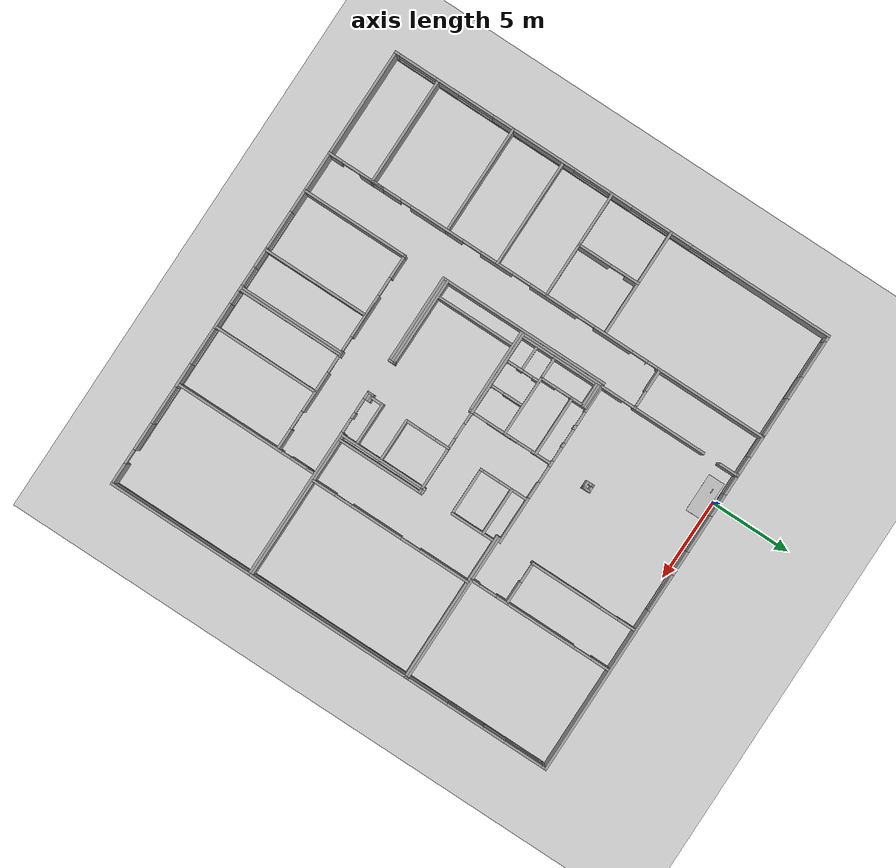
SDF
<?xml version="1.0" ?>

<sdf version="1.6">

  <world name="ur5_world">

    <plugin name="ros_link_attacher_plugin" filename="libgazebo_ros_link_attacher.so"/>
    <gui>
      <camera name="user_camera">
        <pose>1.4 -2.3 1.4 0.0 0.25 1.9</pose>
      </camera>
    </gui>

    <gravity>0 0 -9.81</gravity>

    <physics name="default_physics" default="0" type="ode">
      <max_step_size>0.001</max_step_size>
      <real_time_factor>1</real_time_factor>
      <real_time_update_rate>1000</real_time_update_rate>
    </physics>

    <scene>
      <ambient>0.4 0.4 0.4 1</ambient>
      <background>0.7 0.7 0.7 1</background>
      <shadows>false</shadows>
    </scene>

    <!-- Light Source -->
    <include>
      <uri>model://sun</uri>
    </include>

    <!-- A ground plane -->
    <include>
      <uri>model://ground_plane</uri>
      <pose>0 0 0 0 0 0</pose>
    </include>

    <!-- Table -->
    <model name="modern_table">
      <static>true</static>
      <include>
        <uri>model://modern_table</uri>
         <pose>0 -0.558 0 0 0 -3.1415926535</pose>
      </include>
    </model>

      <!-- Robot Base -->
    <model name="robot_base">
      <static>true</static>
      <include>
        <uri>model://robot_base</uri>
         <pose>0 0 -0.010370 0 0 0</pose>
      </include>
    </model>

    <!-- Kinect camera used for detection -0.58 -0.528 -0.437720 -0.50-->
    <model name="kinect">
      <static>true</static>
      <include>
        <uri>model://kinect</uri>
        <pose>-0.44 -0.50 1.58 1.58 1.57079 0</pose>
      </include>
    </model>
    <include>
      <uri>model://basement</uri>
      <pose>3.106908 -14.007594 0 0 0 0</pose>
    </include>
  </world>
</sdf>

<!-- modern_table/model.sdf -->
<sdf version="1.7">
  <model name="modern_table">
    <static>true</static>
    <link name="link">
      <pose>0 0 0.74 0 0 0</pose>

      <collision name="surface">
        <pose>0 0 -0.015 0 0 0</pose>
        <geometry>
          <box>
            <size>2.35 1 0.03</size>
          </box>
        </geometry>
      </collision>

      <visual name="visual">
        <geometry>
          <mesh>
            <uri>model://modern_table/meshes/modern_table.dae</uri>
          </mesh>
        </geometry>
        <light type="directional" name="some_light">
          <diffuse>0.7 0.7 0.7 0</diffuse>
          <specular>1 1 1 0</specular>
          <direction>-1 -1 -1</direction>
        </light>
      </visual>
    </link>
  </model>
</sdf>

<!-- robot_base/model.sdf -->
<sdf version="1.7">
  <model name="robot_base">
    <static>true</static>
    <link name="link">
      <pose>0 0 0.73 0 0 0</pose>

      <collision name="surface">
        <pose>0 0 -0.015 0 0 0</pose>
        <geometry>
          <box>
            <size>2.35 1 0.03</size>
          </box>
        </geometry>
      </collision>

      <visual name="visual">
        <geometry>
          <mesh>
            <uri>model://robot_base/meshes/robot_base.dae</uri>
          </mesh>
        </geometry>
      </visual>
    </link>
  </model>
</sdf>

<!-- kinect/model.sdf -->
<sdf version="1.5">
  <model name="kinect">
    <pose>0 0 0.036 0 0 0</pose>
    <link name="link">
      <inertial>
        <mass>0.1</mass>
      </inertial>
      <collision name="collision">
        <geometry>
          <box>
            <size>0.073000 0.276000 0.072000</size>
          </box>
        </geometry>
      </collision>
      <visual name="visual">
        <geometry>
          <mesh>
            <uri>model://kinect/meshes/kinect.dae</uri>
          </mesh>
        </geometry>
      </visual>
      <sensor name="camera" type="depth">
        <update_rate>20</update_rate>
        <camera>
          <horizontal_fov>1.047198</horizontal_fov>
          <image>
            <width>640</width>
            <height>480</height>
            <format>R8G8B8</format>
          </image>
          <clip>
            <near>0.05</near>
            <far>3</far>
          </clip>
        </camera>
        <plugin name="camera_plugin" filename="libgazebo_ros_openni_kinect.so">
          <baseline>0.2</baseline>
          <alwaysOn>true</alwaysOn>
          <updateRate>0.0</updateRate>
          <cameraName>camera_ir</cameraName>
          <imageTopicName>/camera/color/image_raw</imageTopicName>
          <cameraInfoTopicName>/camera/color/camera_info</cameraInfoTopicName>
          <depthImageTopicName>/camera/depth/image_raw</depthImageTopicName>
          <depthImageCameraInfoTopicName>/camera/depth/camera_info</depthImageCameraInfoTopicName>
          <pointCloudTopicName>/camera/depth/points</pointCloudTopicName>
          <frameName>base</frameName>
          <pointCloudCutoff>0.5</pointCloudCutoff>
          <pointCloudCutoffMax>3.0</pointCloudCutoffMax>
          <distortionK1>0</distortionK1>
          <distortionK2>0</distortionK2>
          <distortionK3>0</distortionK3>
          <distortionT1>0</distortionT1>
          <distortionT2>0</distortionT2>
          <CxPrime>0</CxPrime>
          <Cx>0</Cx>
          <Cy>0</Cy>
          <focalLength>0</focalLength>
          <hackBaseline>0</hackBaseline>
        </plugin>
      </sensor>
    </link>
  </model>
</sdf>

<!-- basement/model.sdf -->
<sdf version='1.6'>
  <model name='basement'>
    <pose frame=''>-2.12617 -1.77824 0 0 -0 0</pose>
    <link name='Wall_1'>
      <pose frame=''>-14.1254 0.001772 0 0 0 -1.5708</pose>
      <visual name='Wall_1_Visual_0'>
        <pose frame=''>-10.8889 0 1.25 0 -0 0</pose>
        <geometry>
          <box>
            <size>6.72223 0.15 2.5</size>
          </box>
        </geometry>
        <material>
          <script>
            <uri>file://media/materials/scripts/gazebo.material</uri>
            <name>Gazebo/Grey</name>
          </script>
          <ambient>1 1 1 1</ambient>
        </material>
      </visual>
      <collision name='Wall_1_Collision_0'>
        <geometry>
          <box>
            <size>6.72223 0.15 2.5</size>
          </box>
        </geometry>
        <pose frame=''>-10.8889 0 1.25 0 -0 0</pose>
      </collision>
      <visual name='Wall_1_Visual_1'>
        <pose frame=''>3.36112 0 0.25 0 -0 0</pose>
        <geometry>
          <box>
            <size>21.7778 0.15 0.5</size>
          </box>
        </geometry>
        <material>
          <script>
            <uri>file://media/materials/scripts/gazebo.material</uri>
            <name>Gazebo/Grey</name>
          </script>
          <ambient>1 1 1 1</ambient>
        </material>
      </visual>
      <collision name='Wall_1_Collision_1'>
        <geometry>
          <box>
            <size>21.7778 0.15 0.5</size>
          </box>
        </geometry>
        <pose frame=''>3.36112 0 0.25 0 -0 0</pose>
      </collision>
      <visual name='Wall_1_Visual_2'>
        <pose frame=''>-4.48488 0 1.5 0 -0 0</pose>
        <geometry>
          <box>
            <size>1.45334 0.15 2</size>
          </box>
        </geometry>
        <material>
          <script>
            <uri>file://media/materials/scripts/gazebo.material</uri>
            <name>Gazebo/Grey</name>
          </script>
          <ambient>1 1 1 1</ambient>
        </material>
      </visual>
      <collision name='Wall_1_Collision_2'>
        <geometry>
          <box>
            <size>1.45334 0.15 2</size>
          </box>
        </geometry>
        <pose frame=''>-4.48488 0 1.5 0 -0 0</pose>
      </collision>
      <visual name='Wall_1_Visual_3'>
        <pose frame=''>-0.57841 0 1.5 0 -0 0</pose>
        <geometry>
          <box>
            <size>1.45641 0.15 2</size>
          </box>
        </geometry>
        <material>
          <script>
            <uri>file://media/materials/scripts/gazebo.material</uri>
            <name>Gazebo/Grey</name>
          </script>
          <ambient>1 1 1 1</ambient>
        </material>
      </visual>
      <collision name='Wall_1_Collision_3'>
        <geometry>
          <box>
            <size>1.45641 0.15 2</size>
          </box>
        </geometry>
        <pose frame=''>-0.57841 0 1.5 0 -0 0</pose>
      </collision>
      <visual name='Wall_1_Visual_4'>
        <pose frame=''>5.12077 0 1.5 0 -0 0</pose>
        <geometry>
          <box>
            <size>5.31789 0.15 2</size>
          </box>
        </geometry>
        <material>
          <script>
            <uri>file://media/materials/scripts/gazebo.material</uri>
            <name>Gazebo/Grey</name>
          </script>
          <ambient>1 1 1 1</ambient>
        </material>
      </visual>
      <collision name='Wall_1_Collision_4'>
        <geometry>
          <box>
            <size>5.31789 0.15 2</size>
          </box>
        </geometry>
        <pose frame=''>5.12077 0 1.5 0 -0 0</pose>
      </collision>
      <visual name='Wall_1_Visual_5'>
        <pose frame=''>10.7967 0 1.5 0 -0 0</pose>
        <geometry>
          <box>
            <size>1.45641 0.15 2</size>
          </box>
        </geometry>
        <material>
          <script>
            <uri>file://media/materials/scripts/gazebo.material</uri>
            <name>Gazebo/Grey</name>
          </script>
          <ambient>1 1 1 1</ambient>
        </material>
      </visual>
      <collision name='Wall_1_Collision_5'>
        <geometry>
          <box>
            <size>1.45641 0.15 2</size>
          </box>
        </geometry>
        <pose frame=''>10.7967 0 1.5 0 -0 0</pose>
      </collision>
      <visual name='Wall_1_Visual_6'>
        <pose frame=''>14.0784 0 1.5 0 -0 0</pose>
        <geometry>
          <box>
            <size>0.343295 0.15 2</size>
          </box>
        </geometry>
        <material>
          <script>
            <uri>file://media/materials/scripts/gazebo.material</uri>
            <name>Gazebo/Grey</name>
          </script>
          <ambient>1 1 1 1</ambient>
        </material>
      </visual>
      <collision name='Wall_1_Collision_6'>
        <geometry>
          <box>
            <size>0.343295 0.15 2</size>
          </box>
        </geometry>
        <pose frame=''>14.0784 0 1.5 0 -0 0</pose>
      </collision>
      <visual name='Wall_1_Visual_7'>
        <pose frame=''>-6.36966 0 1.9 0 -0 0</pose>
        <geometry>
          <box>
            <size>2.31621 0.15 1.2</size>
          </box>
        </geometry>
        <material>
          <script>
            <uri>file://media/materials/scripts/gazebo.material</uri>
            <name>Gazebo/Grey</name>
          </script>
          <ambient>1 1 1 1</ambient>
        </material>
      </visual>
      <collision name='Wall_1_Collision_7'>
        <geometry>
          <box>
            <size>2.31621 0.15 1.2</size>
          </box>
        </geometry>
        <pose frame=''>-6.36966 0 1.9 0 -0 0</pose>
      </collision>
      <visual name='Wall_1_Visual_8'>
        <pose frame=''>-2.53241 0 1.9 0 -0 0</pose>
        <geometry>
          <box>
            <size>2.4516 0.15 1.2</size>
          </box>
        </geometry>
        <material>
          <script>
            <uri>file://media/materials/scripts/gazebo.material</uri>
            <name>Gazebo/Grey</name>
          </script>
          <ambient>1 1 1 1</ambient>
        </material>
      </visual>
      <collision name='Wall_1_Collision_8'>
        <geometry>
          <box>
            <size>2.4516 0.15 1.2</size>
          </box>
        </geometry>
        <pose frame=''>-2.53241 0 1.9 0 -0 0</pose>
      </collision>
      <visual name='Wall_1_Visual_9'>
        <pose frame=''>1.30581 0 1.9 0 -0 0</pose>
        <geometry>
          <box>
            <size>2.31203 0.15 1.2</size>
          </box>
        </geometry>
        <material>
          <script>
            <uri>file://media/materials/scripts/gazebo.material</uri>
            <name>Gazebo/Grey</name>
          </script>
          <ambient>1 1 1 1</ambient>
        </material>
      </visual>
      <collision name='Wall_1_Collision_9'>
        <geometry>
          <box>
            <size>2.31203 0.15 1.2</size>
          </box>
        </geometry>
        <pose frame=''>1.30581 0 1.9 0 -0 0</pose>
      </collision>
      <visual name='Wall_1_Visual_10'>
        <pose frame=''>8.9241 0 1.9 0 -0 0</pose>
        <geometry>
          <box>
            <size>2.28877 0.15 1.2</size>
          </box>
        </geometry>
        <material>
          <script>
            <uri>file://media/materials/scripts/gazebo.material</uri>
            <name>Gazebo/Grey</name>
          </script>
          <ambient>1 1 1 1</ambient>
        </material>
      </visual>
      <collision name='Wall_1_Collision_10'>
        <geometry>
          <box>
            <size>2.28877 0.15 1.2</size>
          </box>
        </geometry>
        <pose frame=''>8.9241 0 1.9 0 -0 0</pose>
      </collision>
      <visual name='Wall_1_Visual_11'>
        <pose frame=''>12.7158 0 1.9 0 -0 0</pose>
        <geometry>
          <box>
            <size>2.38181 0.15 1.2</size>
          </box>
        </geometry>
        <material>
          <script>
            <uri>file://media/materials/scripts/gazebo.material</uri>
            <name>Gazebo/Grey</name>
          </script>
          <ambient>1 1 1 1</ambient>
        </material>
      </visual>
      <collision name='Wall_1_Collision_11'>
        <geometry>
          <box>
            <size>2.38181 0.15 1.2</size>
          </box>
        </geometry>
        <pose frame=''>12.7158 0 1.9 0 -0 0</pose>
      </collision>
    </link>
    <link name='Wall_100'>
      <pose frame=''>8.19919 -5.19776 0 0 -0 0</pose>
      <visual name='Wall_100_Visual_0'>
        <pose frame=''>-5.7562 0 1.25 0 -0 0</pose>
        <geometry>
          <box>
            <size>0.487607 0.15 2.5</size>
          </box>
        </geometry>
        <material>
          <script>
            <uri>file://media/materials/scripts/gazebo.material</uri>
            <name>Gazebo/Grey</name>
          </script>
          <ambient>1 1 1 1</ambient>
        </material>
      </visual>
      <collision name='Wall_100_Collision_0'>
        <geometry>
          <box>
            <size>0.487607 0.15 2.5</size>
          </box>
        </geometry>
        <pose frame=''>-5.7562 0 1.25 0 -0 0</pose>
      </collision>
      <visual name='Wall_100_Visual_1'>
        <pose frame=''>-4.42761 0 1.25 0 -0 0</pose>
        <geometry>
          <box>
            <size>0.369565 0.15 2.5</size>
          </box>
        </geometry>
        <material>
          <script>
            <uri>file://media/materials/scripts/gazebo.material</uri>
            <name>Gazebo/Grey</name>
          </script>
          <ambient>1 1 1 1</ambient>
        </material>
      </visual>
      <collision name='Wall_100_Collision_1'>
        <geometry>
          <box>
            <size>0.369565 0.15 2.5</size>
          </box>
        </geometry>
        <pose frame=''>-4.42761 0 1.25 0 -0 0</pose>
      </collision>
      <visual name='Wall_100_Visual_2'>
        <pose frame=''>1.32859 0 1.25 0 -0 0</pose>
        <geometry>
          <box>
            <size>9.34283 0.15 2.5</size>
          </box>
        </geometry>
        <material>
          <script>
            <uri>file://media/materials/scripts/gazebo.material</uri>
            <name>Gazebo/Grey</name>
          </script>
          <ambient>1 1 1 1</ambient>
        </material>
      </visual>
      <collision name='Wall_100_Collision_2'>
        <geometry>
          <box>
            <size>9.34283 0.15 2.5</size>
          </box>
        </geometry>
        <pose frame=''>1.32859 0 1.25 0 -0 0</pose>
      </collision>
      <visual name='Wall_100_Visual_3'>
        <pose frame=''>-5.06239 0 2.25 0 -0 0</pose>
        <geometry>
          <box>
            <size>0.9 0.15 0.5</size>
          </box>
        </geometry>
        <material>
          <script>
            <uri>file://media/materials/scripts/gazebo.material</uri>
            <name>Gazebo/Grey</name>
          </script>
          <ambient>1 1 1 1</ambient>
        </material>
      </visual>
      <collision name='Wall_100_Collision_3'>
        <geometry>
          <box>
            <size>0.9 0.15 0.5</size>
          </box>
        </geometry>
        <pose frame=''>-5.06239 0 2.25 0 -0 0</pose>
      </collision>
      <visual name='Wall_100_Visual_4'>
        <pose frame=''>-3.79283 0 2.25 0 -0 0</pose>
        <geometry>
          <box>
            <size>0.9 0.15 0.5</size>
          </box>
        </geometry>
        <material>
          <script>
            <uri>file://media/materials/scripts/gazebo.material</uri>
            <name>Gazebo/Grey</name>
          </script>
          <ambient>1 1 1 1</ambient>
        </material>
      </visual>
      <collision name='Wall_100_Collision_4'>
        <geometry>
          <box>
            <size>0.9 0.15 0.5</size>
          </box>
        </geometry>
        <pose frame=''>-3.79283 0 2.25 0 -0 0</pose>
      </collision>
    </link>
    <link name='Wall_102'>
      <collision name='Wall_102_Collision'>
        <geometry>
          <box>
            <size>9.25 0.15 2.5</size>
          </box>
        </geometry>
        <pose frame=''>0 0 1.25 0 -0 0</pose>
      </collision>
      <visual name='Wall_102_Visual'>
        <pose frame=''>0 0 1.25 0 -0 0</pose>
        <geometry>
          <box>
            <size>9.25 0.15 2.5</size>
          </box>
        </geometry>
        <material>
          <script>
            <uri>file://media/materials/scripts/gazebo.material</uri>
            <name>Gazebo/Grey</name>
          </script>
          <ambient>1 1 1 1</ambient>
        </material>
      </visual>
      <pose frame=''>9.51475 -5.05392 0 0 -0 0</pose>
    </link>
    <link name='Wall_104'>
      <collision name='Wall_104_Collision'>
        <geometry>
          <box>
            <size>5.5 0.15 2.5</size>
          </box>
        </geometry>
        <pose frame=''>0 0 1.25 0 -0 0</pose>
      </collision>
      <visual name='Wall_104_Visual'>
        <pose frame=''>0 0 1.25 0 -0 0</pose>
        <geometry>
          <box>
            <size>5.5 0.15 2.5</size>
          </box>
        </geometry>
        <material>
          <script>
            <uri>file://media/materials/scripts/gazebo.material</uri>
            <name>Gazebo/Grey</name>
          </script>
          <ambient>1 1 1 1</ambient>
        </material>
      </visual>
      <pose frame=''>5.28935 -2.40756 0 0 0 -1.5708</pose>
    </link>
    <link name='Wall_108'>
      <pose frame=''>2.7255 0.139626 0 0 -0 0</pose>
      <visual name='Wall_108_Visual_0'>
        <pose frame=''>-2.26972 0 1.25 0 -0 0</pose>
        <geometry>
          <box>
            <size>0.710554 0.15 2.5</size>
          </box>
        </geometry>
        <material>
          <script>
            <uri>file://media/materials/scripts/gazebo.material</uri>
            <name>Gazebo/Grey</name>
          </script>
          <ambient>1 1 1 1</ambient>
        </material>
      </visual>
      <collision name='Wall_108_Collision_0'>
        <geometry>
          <box>
            <size>0.710554 0.15 2.5</size>
          </box>
        </geometry>
        <pose frame=''>-2.26972 0 1.25 0 -0 0</pose>
      </collision>
      <visual name='Wall_108_Visual_1'>
        <pose frame=''>0.840079 0 1.25 0 -0 0</pose>
        <geometry>
          <box>
            <size>3.56984 0.15 2.5</size>
          </box>
        </geometry>
        <material>
          <script>
            <uri>file://media/materials/scripts/gazebo.material</uri>
            <name>Gazebo/Grey</name>
          </script>
          <ambient>1 1 1 1</ambient>
        </material>
      </visual>
      <collision name='Wall_108_Collision_1'>
        <geometry>
          <box>
            <size>3.56984 0.15 2.5</size>
          </box>
        </geometry>
        <pose frame=''>0.840079 0 1.25 0 -0 0</pose>
      </collision>
      <visual name='Wall_108_Visual_2'>
        <pose frame=''>-1.42964 0 2.25 0 -0 0</pose>
        <geometry>
          <box>
            <size>0.969605 0.15 0.5</size>
          </box>
        </geometry>
        <material>
          <script>
            <uri>file://media/materials/scripts/gazebo.material</uri>
            <name>Gazebo/Grey</name>
          </script>
          <ambient>1 1 1 1</ambient>
        </material>
      </visual>
      <collision name='Wall_108_Collision_2'>
        <geometry>
          <box>
            <size>0.969605 0.15 0.5</size>
          </box>
        </geometry>
        <pose frame=''>-1.42964 0 2.25 0 -0 0</pose>
      </collision>
    </link>
    <link name='Wall_11'>
      <collision name='Wall_11_Collision'>
        <geometry>
          <box>
            <size>6.75 0.15 2.5</size>
          </box>
        </geometry>
        <pose frame=''>0 0 1.25 0 -0 0</pose>
      </collision>
      <visual name='Wall_11_Visual'>
        <pose frame=''>0 0 1.25 0 -0 0</pose>
        <geometry>
          <box>
            <size>6.75 0.15 2.5</size>
          </box>
        </geometry>
        <material>
          <script>
            <uri>file://media/materials/scripts/gazebo.material</uri>
            <name>Gazebo/Grey</name>
          </script>
          <ambient>1 1 1 1</ambient>
        </material>
      </visual>
      <pose frame=''>-10.8091 -11.3705 0 0 -0 0</pose>
    </link>
    <link name='Wall_112'>
      <collision name='Wall_112_Collision'>
        <geometry>
          <box>
            <size>5.5 0.15 2.5</size>
          </box>
        </geometry>
        <pose frame=''>0 0 1.25 0 -0 0</pose>
      </collision>
      <visual name='Wall_112_Visual'>
        <pose frame=''>0 0 1.25 0 -0 0</pose>
        <geometry>
          <box>
            <size>5.5 0.15 2.5</size>
          </box>
        </geometry>
        <material>
          <script>
            <uri>file://media/materials/scripts/gazebo.material</uri>
            <name>Gazebo/Grey</name>
          </script>
          <ambient>1 1 1 1</ambient>
        </material>
      </visual>
      <pose frame=''>5.00796 -2.4103 0 0 0 -1.5708</pose>
    </link>
    <link name='Wall_116'>
      <collision name='Wall_116_Collision'>
        <geometry>
          <box>
            <size>0.4 0.15 2.5</size>
          </box>
        </geometry>
        <pose frame=''>0 0 1.25 0 -0 0</pose>
      </collision>
      <visual name='Wall_116_Visual'>
        <pose frame=''>0 0 1.25 0 -0 0</pose>
        <geometry>
          <box>
            <size>0.4 0.15 2.5</size>
          </box>
        </geometry>
        <material>
          <script>
            <uri>file://media/materials/scripts/gazebo.material</uri>
            <name>Gazebo/Grey</name>
          </script>
          <ambient>1 1 1 1</ambient>
        </material>
      </visual>
      <pose frame=''>5.13257 0.268093 0 0 -0 0</pose>
    </link>
    <link name='Wall_118'>
      <pose frame=''>2.41948 -1.1745 0 0 -0 1.5708</pose>
      <visual name='Wall_118_Visual_0'>
        <pose frame=''>-0.97086 0 1.25 0 -0 0</pose>
        <geometry>
          <box>
            <size>0.808281 0.15 2.5</size>
          </box>
        </geometry>
        <material>
          <script>
            <uri>file://media/materials/scripts/gazebo.material</uri>
            <name>Gazebo/Grey</name>
          </script>
          <ambient>1 1 1 1</ambient>
        </material>
      </visual>
      <collision name='Wall_118_Collision_0'>
        <geometry>
          <box>
            <size>0.808281 0.15 2.5</size>
          </box>
        </geometry>
        <pose frame=''>-0.97086 0 1.25 0 -0 0</pose>
      </collision>
      <visual name='Wall_118_Visual_1'>
        <pose frame=''>0.913802 0 1.25 0 -0 0</pose>
        <geometry>
          <box>
            <size>0.922397 0.15 2.5</size>
          </box>
        </geometry>
        <material>
          <script>
            <uri>file://media/materials/scripts/gazebo.material</uri>
            <name>Gazebo/Grey</name>
          </script>
          <ambient>1 1 1 1</ambient>
        </material>
      </visual>
      <collision name='Wall_118_Collision_1'>
        <geometry>
          <box>
            <size>0.922397 0.15 2.5</size>
          </box>
        </geometry>
        <pose frame=''>0.913802 0 1.25 0 -0 0</pose>
      </collision>
      <visual name='Wall_118_Visual_2'>
        <pose frame=''>-0.057058 0 2.25 0 -0 0</pose>
        <geometry>
          <box>
            <size>1.01932 0.15 0.5</size>
          </box>
        </geometry>
        <material>
          <script>
            <uri>file://media/materials/scripts/gazebo.material</uri>
            <name>Gazebo/Grey</name>
          </script>
          <ambient>1 1 1 1</ambient>
        </material>
      </visual>
      <collision name='Wall_118_Collision_2'>
        <geometry>
          <box>
            <size>1.01932 0.15 0.5</size>
          </box>
        </geometry>
        <pose frame=''>-0.057058 0 2.25 0 -0 0</pose>
      </collision>
    </link>
    <link name='Wall_120'>
      <collision name='Wall_120_Collision'>
        <geometry>
          <box>
            <size>2.75 0.15 2.5</size>
          </box>
        </geometry>
        <pose frame=''>0 0 1.25 0 -0 0</pose>
      </collision>
      <visual name='Wall_120_Visual'>
        <pose frame=''>0 0 1.25 0 -0 0</pose>
        <geometry>
          <box>
            <size>2.75 0.15 2.5</size>
          </box>
        </geometry>
        <material>
          <script>
            <uri>file://media/materials/scripts/gazebo.material</uri>
            <name>Gazebo/Grey</name>
          </script>
          <ambient>1 1 1 1</ambient>
        </material>
      </visual>
      <pose frame=''>3.71948 -2.60376 0 0 -0 0</pose>
    </link>
    <link name='Wall_122'>
      <collision name='Wall_122_Collision'>
        <geometry>
          <box>
            <size>2.75 0.15 2.5</size>
          </box>
        </geometry>
        <pose frame=''>0 0 1.25 0 -0 0</pose>
      </collision>
      <visual name='Wall_122_Visual'>
        <pose frame=''>0 0 1.25 0 -0 0</pose>
        <geometry>
          <box>
            <size>2.75 0.15 2.5</size>
          </box>
        </geometry>
        <material>
          <script>
            <uri>file://media/materials/scripts/gazebo.material</uri>
            <name>Gazebo/Grey</name>
          </script>
          <ambient>1 1 1 1</ambient>
        </material>
      </visual>
      <pose frame=''>3.71502 -4.18637 0 0 -0 0</pose>
    </link>
    <link name='Wall_124'>
      <collision name='Wall_124_Collision'>
        <geometry>
          <box>
            <size>0.5 0.15 2.5</size>
          </box>
        </geometry>
        <pose frame=''>0 0 1.25 0 -0 0</pose>
      </collision>
      <visual name='Wall_124_Visual'>
        <pose frame=''>0 0 1.25 0 -0 0</pose>
        <geometry>
          <box>
            <size>0.5 0.15 2.5</size>
          </box>
        </geometry>
        <material>
          <script>
            <uri>file://media/materials/scripts/gazebo.material</uri>
            <name>Gazebo/Grey</name>
          </script>
          <ambient>1 1 1 1</ambient>
        </material>
      </visual>
      <pose frame=''>2.45081 -4.90231 0 0 -0 0</pose>
    </link>
    <link name='Wall_126'>
      <collision name='Wall_126_Collision'>
        <geometry>
          <box>
            <size>0.4 0.15 2.5</size>
          </box>
        </geometry>
        <pose frame=''>0 0 1.25 0 -0 0</pose>
      </collision>
      <visual name='Wall_126_Visual'>
        <pose frame=''>0 0 1.25 0 -0 0</pose>
        <geometry>
          <box>
            <size>0.4 0.15 2.5</size>
          </box>
        </geometry>
        <material>
          <script>
            <uri>file://media/materials/scripts/gazebo.material</uri>
            <name>Gazebo/Grey</name>
          </script>
          <ambient>1 1 1 1</ambient>
        </material>
      </visual>
      <pose frame=''>2.27581 -5.05714 0 0 0 -1.5708</pose>
    </link>
    <link name='Wall_128'>
      <collision name='Wall_128_Collision'>
        <geometry>
          <box>
            <size>0.75 0.15 2.5</size>
          </box>
        </geometry>
        <pose frame=''>0 0 1.25 0 -0 0</pose>
      </collision>
      <visual name='Wall_128_Visual'>
        <pose frame=''>0 0 1.25 0 -0 0</pose>
        <geometry>
          <box>
            <size>0.75 0.15 2.5</size>
          </box>
        </geometry>
        <material>
          <script>
            <uri>file://media/materials/scripts/gazebo.material</uri>
            <name>Gazebo/Grey</name>
          </script>
          <ambient>1 1 1 1</ambient>
        </material>
      </visual>
      <pose frame=''>2.41502 -4.54603 0 0 0 -1.5708</pose>
    </link>
    <link name='Wall_13'>
      <collision name='Wall_13_Collision'>
        <geometry>
          <box>
            <size>6.75 0.15 2.5</size>
          </box>
        </geometry>
        <pose frame=''>0 0 1.25 0 -0 0</pose>
      </collision>
      <visual name='Wall_13_Visual'>
        <pose frame=''>0 0 1.25 0 -0 0</pose>
        <geometry>
          <box>
            <size>6.75 0.15 2.5</size>
          </box>
        </geometry>
        <material>
          <script>
            <uri>file://media/materials/scripts/gazebo.material</uri>
            <name>Gazebo/Grey</name>
          </script>
          <ambient>1 1 1 1</ambient>
        </material>
      </visual>
      <pose frame=''>-10.8096 -6.47351 0 0 -0 0</pose>
    </link>
    <link name='Wall_130'>
      <pose frame=''>7.59342 -9.67316 0 0 -0 1.5708</pose>
      <visual name='Wall_130_Visual_0'>
        <pose frame=''>-1.10011 0 1.25 0 -0 0</pose>
        <geometry>
          <box>
            <size>6.79978 0.15 2.5</size>
          </box>
        </geometry>
        <material>
          <script>
            <uri>file://media/materials/scripts/gazebo.material</uri>
            <name>Gazebo/Grey</name>
          </script>
          <ambient>1 1 1 1</ambient>
        </material>
      </visual>
      <collision name='Wall_130_Collision_0'>
        <geometry>
          <box>
            <size>6.79978 0.15 2.5</size>
          </box>
        </geometry>
        <pose frame=''>-1.10011 0 1.25 0 -0 0</pose>
      </collision>
      <visual name='Wall_130_Visual_1'>
        <pose frame=''>3.69951 0 1.25 0 -0 0</pose>
        <geometry>
          <box>
            <size>1.60098 0.15 2.5</size>
          </box>
        </geometry>
        <material>
          <script>
            <uri>file://media/materials/scripts/gazebo.material</uri>
            <name>Gazebo/Grey</name>
          </script>
          <ambient>1 1 1 1</ambient>
        </material>
      </visual>
      <collision name='Wall_130_Collision_1'>
        <geometry>
          <box>
            <size>1.60098 0.15 2.5</size>
          </box>
        </geometry>
        <pose frame=''>3.69951 0 1.25 0 -0 0</pose>
      </collision>
      <visual name='Wall_130_Visual_2'>
        <pose frame=''>4.21195 0 1.25 0 -0 0</pose>
        <geometry>
          <box>
            <size>0.576095 0.15 2.5</size>
          </box>
        </geometry>
        <material>
          <script>
            <uri>file://media/materials/scripts/gazebo.material</uri>
            <name>Gazebo/Grey</name>
          </script>
          <ambient>1 1 1 1</ambient>
        </material>
      </visual>
      <collision name='Wall_130_Collision_2'>
        <geometry>
          <box>
            <size>0.576095 0.15 2.5</size>
          </box>
        </geometry>
        <pose frame=''>4.21195 0 1.25 0 -0 0</pose>
      </collision>
      <visual name='Wall_130_Visual_3'>
        <pose frame=''>2.59646 0 2.25 0 -0 0</pose>
        <geometry>
          <box>
            <size>0.593362 0.15 0.5</size>
          </box>
        </geometry>
        <material>
          <script>
            <uri>file://media/materials/scripts/gazebo.material</uri>
            <name>Gazebo/Grey</name>
          </script>
          <ambient>1 1 1 1</ambient>
        </material>
      </visual>
      <collision name='Wall_130_Collision_3'>
        <geometry>
          <box>
            <size>0.593362 0.15 0.5</size>
          </box>
        </geometry>
        <pose frame=''>2.59646 0 2.25 0 -0 0</pose>
      </collision>
    </link>
    <link name='Wall_132'>
      <collision name='Wall_132_Collision'>
        <geometry>
          <box>
            <size>6.6 0.15 2.5</size>
          </box>
        </geometry>
        <pose frame=''>0 0 1.25 0 -0 0</pose>
      </collision>
      <visual name='Wall_132_Visual'>
        <pose frame=''>0 0 1.25 0 -0 0</pose>
        <geometry>
          <box>
            <size>6.6 0.15 2.5</size>
          </box>
        </geometry>
        <material>
          <script>
            <uri>file://media/materials/scripts/gazebo.material</uri>
            <name>Gazebo/Grey</name>
          </script>
          <ambient>1 1 1 1</ambient>
        </material>
      </visual>
      <pose frame=''>-5.06165 -10.8664 0 0 0 -1.5708</pose>
    </link>
    <link name='Wall_134'>
      <pose frame=''>1.23835 -7.64141 0 0 -0 0</pose>
      <visual name='Wall_134_Visual_0'>
        <pose frame=''>-5.62659 0 1.25 0 -0 0</pose>
        <geometry>
          <box>
            <size>1.49682 0.15 2.5</size>
          </box>
        </geometry>
        <material>
          <script>
            <uri>file://media/materials/scripts/gazebo.material</uri>
            <name>Gazebo/Grey</name>
          </script>
          <ambient>1 1 1 1</ambient>
        </material>
      </visual>
      <collision name='Wall_134_Collision_0'>
        <geometry>
          <box>
            <size>1.49682 0.15 2.5</size>
          </box>
        </geometry>
        <pose frame=''>-5.62659 0 1.25 0 -0 0</pose>
      </collision>
      <visual name='Wall_134_Visual_1'>
        <pose frame=''>-2.35576 0 1.25 0 -0 0</pose>
        <geometry>
          <box>
            <size>2.70875 0.15 2.5</size>
          </box>
        </geometry>
        <material>
          <script>
            <uri>file://media/materials/scripts/gazebo.material</uri>
            <name>Gazebo/Grey</name>
          </script>
          <ambient>1 1 1 1</ambient>
        </material>
      </visual>
      <collision name='Wall_134_Collision_1'>
        <geometry>
          <box>
            <size>2.70875 0.15 2.5</size>
          </box>
        </geometry>
        <pose frame=''>-2.35576 0 1.25 0 -0 0</pose>
      </collision>
      <visual name='Wall_134_Visual_2'>
        <pose frame=''>-2.12152 0 1.25 0 -0 0</pose>
        <geometry>
          <box>
            <size>2.24027 0.15 2.5</size>
          </box>
        </geometry>
        <material>
          <script>
            <uri>file://media/materials/scripts/gazebo.material</uri>
            <name>Gazebo/Grey</name>
          </script>
          <ambient>1 1 1 1</ambient>
        </material>
      </visual>
      <collision name='Wall_134_Collision_2'>
        <geometry>
          <box>
            <size>2.24027 0.15 2.5</size>
          </box>
        </geometry>
        <pose frame=''>-2.12152 0 1.25 0 -0 0</pose>
      </collision>
      <visual name='Wall_134_Visual_3'>
        <pose frame=''>0.087487 0 1.25 0 -0 0</pose>
        <geometry>
          <box>
            <size>0.377744 0.15 2.5</size>
          </box>
        </geometry>
        <material>
          <script>
            <uri>file://media/materials/scripts/gazebo.material</uri>
            <name>Gazebo/Grey</name>
          </script>
          <ambient>1 1 1 1</ambient>
        </material>
      </visual>
      <collision name='Wall_134_Collision_3'>
        <geometry>
          <box>
            <size>0.377744 0.15 2.5</size>
          </box>
        </geometry>
        <pose frame=''>0.087487 0 1.25 0 -0 0</pose>
      </collision>
      <visual name='Wall_134_Visual_4'>
        <pose frame=''>2.60072 0 1.25 0 -0 0</pose>
        <geometry>
          <box>
            <size>2.55041 0.15 2.5</size>
          </box>
        </geometry>
        <material>
          <script>
            <uri>file://media/materials/scripts/gazebo.material</uri>
            <name>Gazebo/Grey</name>
          </script>
          <ambient>1 1 1 1</ambient>
        </material>
      </visual>
      <collision name='Wall_134_Collision_4'>
        <geometry>
          <box>
            <size>2.55041 0.15 2.5</size>
          </box>
        </geometry>
        <pose frame=''>2.60072 0 1.25 0 -0 0</pose>
      </collision>
      <visual name='Wall_134_Visual_5'>
        <pose frame=''>5.69975 0 1.25 0 -0 0</pose>
        <geometry>
          <box>
            <size>1.35049 0.15 2.5</size>
          </box>
        </geometry>
        <material>
          <script>
            <uri>file://media/materials/scripts/gazebo.material</uri>
            <name>Gazebo/Grey</name>
          </script>
          <ambient>1 1 1 1</ambient>
        </material>
      </visual>
      <collision name='Wall_134_Collision_5'>
        <geometry>
          <box>
            <size>1.35049 0.15 2.5</size>
          </box>
        </geometry>
        <pose frame=''>5.69975 0 1.25 0 -0 0</pose>
      </collision>
      <visual name='Wall_134_Visual_6'>
        <pose frame=''>-4.29684 0 2.25 0 -0 0</pose>
        <geometry>
          <box>
            <size>1.16267 0.15 0.5</size>
          </box>
        </geometry>
        <material>
          <script>
            <uri>file://media/materials/scripts/gazebo.material</uri>
            <name>Gazebo/Grey</name>
          </script>
          <ambient>1 1 1 1</ambient>
        </material>
      </visual>
      <collision name='Wall_134_Collision_6'>
        <geometry>
          <box>
            <size>1.16267 0.15 0.5</size>
          </box>
        </geometry>
        <pose frame=''>-4.29684 0 2.25 0 -0 0</pose>
      </collision>
      <visual name='Wall_134_Visual_7'>
        <pose frame=''>-0.551385 0 2.25 0 -0 0</pose>
        <geometry>
          <box>
            <size>0.9 0.15 0.5</size>
          </box>
        </geometry>
        <material>
          <script>
            <uri>file://media/materials/scripts/gazebo.material</uri>
            <name>Gazebo/Grey</name>
          </script>
          <ambient>1 1 1 1</ambient>
        </material>
      </visual>
      <collision name='Wall_134_Collision_7'>
        <geometry>
          <box>
            <size>0.9 0.15 0.5</size>
          </box>
        </geometry>
        <pose frame=''>-0.551385 0 2.25 0 -0 0</pose>
      </collision>
      <visual name='Wall_134_Visual_8'>
        <pose frame=''>-0.551385 0 2.25 0 -0 0</pose>
        <geometry>
          <box>
            <size>0.9 0.15 0.5</size>
          </box>
        </geometry>
        <material>
          <script>
            <uri>file://media/materials/scripts/gazebo.material</uri>
            <name>Gazebo/Grey</name>
          </script>
          <ambient>1 1 1 1</ambient>
        </material>
      </visual>
      <collision name='Wall_134_Collision_8'>
        <geometry>
          <box>
            <size>0.9 0.15 0.5</size>
          </box>
        </geometry>
        <pose frame=''>-0.551385 0 2.25 0 -0 0</pose>
      </collision>
      <visual name='Wall_134_Visual_9'>
        <pose frame=''>0.800936 0 2.25 0 -0 0</pose>
        <geometry>
          <box>
            <size>1.04915 0.15 0.5</size>
          </box>
        </geometry>
        <material>
          <script>
            <uri>file://media/materials/scripts/gazebo.material</uri>
            <name>Gazebo/Grey</name>
          </script>
          <ambient>1 1 1 1</ambient>
        </material>
      </visual>
      <collision name='Wall_134_Collision_9'>
        <geometry>
          <box>
            <size>1.04915 0.15 0.5</size>
          </box>
        </geometry>
        <pose frame=''>0.800936 0 2.25 0 -0 0</pose>
      </collision>
      <visual name='Wall_134_Visual_10'>
        <pose frame=''>4.45021 0 2.25 0 -0 0</pose>
        <geometry>
          <box>
            <size>1.14859 0.15 0.5</size>
          </box>
        </geometry>
        <material>
          <script>
            <uri>file://media/materials/scripts/gazebo.material</uri>
            <name>Gazebo/Grey</name>
          </script>
          <ambient>1 1 1 1</ambient>
        </material>
      </visual>
      <collision name='Wall_134_Collision_10'>
        <geometry>
          <box>
            <size>1.14859 0.15 0.5</size>
          </box>
        </geometry>
        <pose frame=''>4.45021 0 2.25 0 -0 0</pose>
      </collision>
    </link>
    <link name='Wall_136'>
      <collision name='Wall_136_Collision'>
        <geometry>
          <box>
            <size>6.5 0.15 2.5</size>
          </box>
        </geometry>
        <pose frame=''>0 0 1.25 0 -0 0</pose>
      </collision>
      <visual name='Wall_136_Visual'>
        <pose frame=''>0 0 1.25 0 -0 0</pose>
        <geometry>
          <box>
            <size>6.5 0.15 2.5</size>
          </box>
        </geometry>
        <material>
          <script>
            <uri>file://media/materials/scripts/gazebo.material</uri>
            <name>Gazebo/Grey</name>
          </script>
          <ambient>1 1 1 1</ambient>
        </material>
      </visual>
      <pose frame=''>-1.17554 -10.926 0 0 -0 1.5708</pose>
    </link>
    <link name='Wall_138'>
      <collision name='Wall_138_Collision'>
        <geometry>
          <box>
            <size>6.5 0.15 2.5</size>
          </box>
        </geometry>
        <pose frame=''>0 0 1.25 0 -0 0</pose>
      </collision>
      <visual name='Wall_138_Visual'>
        <pose frame=''>0 0 1.25 0 -0 0</pose>
        <geometry>
          <box>
            <size>6.5 0.15 2.5</size>
          </box>
        </geometry>
        <material>
          <script>
            <uri>file://media/materials/scripts/gazebo.material</uri>
            <name>Gazebo/Grey</name>
          </script>
          <ambient>1 1 1 1</ambient>
        </material>
      </visual>
      <pose frame=''>1.2636 -10.87 0 0 -0 1.5708</pose>
    </link>
    <link name='Wall_140'>
      <collision name='Wall_140_Collision'>
        <geometry>
          <box>
            <size>6.5 0.15 2.5</size>
          </box>
        </geometry>
        <pose frame=''>0 0 1.25 0 -0 0</pose>
      </collision>
      <visual name='Wall_140_Visual'>
        <pose frame=''>0 0 1.25 0 -0 0</pose>
        <geometry>
          <box>
            <size>6.5 0.15 2.5</size>
          </box>
        </geometry>
        <material>
          <script>
            <uri>file://media/materials/scripts/gazebo.material</uri>
            <name>Gazebo/Grey</name>
          </script>
          <ambient>1 1 1 1</ambient>
        </material>
      </visual>
      <pose frame=''>1.40771 -10.8804 0 0 0 -1.5708</pose>
    </link>
    <link name='Wall_142'>
      <collision name='Wall_142_Collision'>
        <geometry>
          <box>
            <size>6.5 0.15 2.5</size>
          </box>
        </geometry>
        <pose frame=''>0 0 1.25 0 -0 0</pose>
      </collision>
      <visual name='Wall_142_Visual'>
        <pose frame=''>0 0 1.25 0 -0 0</pose>
        <geometry>
          <box>
            <size>6.5 0.15 2.5</size>
          </box>
        </geometry>
        <material>
          <script>
            <uri>file://media/materials/scripts/gazebo.material</uri>
            <name>Gazebo/Grey</name>
          </script>
          <ambient>1 1 1 1</ambient>
        </material>
      </visual>
      <pose frame=''>3.84111 -10.8753 0 0 0 -1.5708</pose>
    </link>
    <link name='Wall_144'>
      <collision name='Wall_144_Collision'>
        <geometry>
          <box>
            <size>5.25 0.15 2.5</size>
          </box>
        </geometry>
        <pose frame=''>0 0 1.25 0 -0 0</pose>
      </collision>
      <visual name='Wall_144_Visual'>
        <pose frame=''>0 0 1.25 0 -0 0</pose>
        <geometry>
          <box>
            <size>5.25 0.15 2.5</size>
          </box>
        </geometry>
        <material>
          <script>
            <uri>file://media/materials/scripts/gazebo.material</uri>
            <name>Gazebo/Grey</name>
          </script>
          <ambient>1 1 1 1</ambient>
        </material>
      </visual>
      <pose frame=''>-2.51608 -5.05083 0 0 -0 0</pose>
    </link>
    <link name='Wall_146'>
      <collision name='Wall_146_Collision'>
        <geometry>
          <box>
            <size>5.25 0.15 2.5</size>
          </box>
        </geometry>
        <pose frame=''>0 0 1.25 0 -0 0</pose>
      </collision>
      <visual name='Wall_146_Visual'>
        <pose frame=''>0 0 1.25 0 -0 0</pose>
        <geometry>
          <box>
            <size>5.25 0.15 2.5</size>
          </box>
        </geometry>
        <material>
          <script>
            <uri>file://media/materials/scripts/gazebo.material</uri>
            <name>Gazebo/Grey</name>
          </script>
          <ambient>1 1 1 1</ambient>
        </material>
      </visual>
      <pose frame=''>-5.04892 2.61682 0 0 -0 1.5708</pose>
    </link>
    <link name='Wall_148'>
      <collision name='Wall_148_Collision'>
        <geometry>
          <box>
            <size>1.5 0.15 2.5</size>
          </box>
        </geometry>
        <pose frame=''>0 0 1.25 0 -0 0</pose>
      </collision>
      <visual name='Wall_148_Visual'>
        <pose frame=''>0 0 1.25 0 -0 0</pose>
        <geometry>
          <box>
            <size>1.5 0.15 2.5</size>
          </box>
        </geometry>
        <material>
          <script>
            <uri>file://media/materials/scripts/gazebo.material</uri>
            <name>Gazebo/Grey</name>
          </script>
          <ambient>1 1 1 1</ambient>
        </material>
      </visual>
      <pose frame=''>-4.23612 5.13065 0 0 -0 0</pose>
    </link>
    <link name='Wall_15'>
      <collision name='Wall_15_Collision'>
        <geometry>
          <box>
            <size>6.75 0.15 2.5</size>
          </box>
        </geometry>
        <pose frame=''>0 0 1.25 0 -0 0</pose>
      </collision>
      <visual name='Wall_15_Visual'>
        <pose frame=''>0 0 1.25 0 -0 0</pose>
        <geometry>
          <box>
            <size>6.75 0.15 2.5</size>
          </box>
        </geometry>
        <material>
          <script>
            <uri>file://media/materials/scripts/gazebo.material</uri>
            <name>Gazebo/Grey</name>
          </script>
          <ambient>1 1 1 1</ambient>
        </material>
      </visual>
      <pose frame=''>-10.8156 -3.17919 0 0 -0 0</pose>
    </link>
    <link name='Wall_150'>
      <collision name='Wall_150_Collision'>
        <geometry>
          <box>
            <size>1.5 0.15 2.5</size>
          </box>
        </geometry>
        <pose frame=''>0 0 1.25 0 -0 0</pose>
      </collision>
      <visual name='Wall_150_Visual'>
        <pose frame=''>0 0 1.25 0 -0 0</pose>
        <geometry>
          <box>
            <size>1.5 0.15 2.5</size>
          </box>
        </geometry>
        <material>
          <script>
            <uri>file://media/materials/scripts/gazebo.material</uri>
            <name>Gazebo/Grey</name>
          </script>
          <ambient>1 1 1 1</ambient>
        </material>
      </visual>
      <pose frame=''>-4.23669 5.20302 0 0 -0 0</pose>
    </link>
    <link name='Wall_152'>
      <collision name='Wall_152_Collision'>
        <geometry>
          <box>
            <size>5.25 0.15 2.5</size>
          </box>
        </geometry>
        <pose frame=''>0 0 1.25 0 -0 0</pose>
      </collision>
      <visual name='Wall_152_Visual'>
        <pose frame=''>0 0 1.25 0 -0 0</pose>
        <geometry>
          <box>
            <size>5.25 0.15 2.5</size>
          </box>
        </geometry>
        <material>
          <script>
            <uri>file://media/materials/scripts/gazebo.material</uri>
            <name>Gazebo/Grey</name>
          </script>
          <ambient>1 1 1 1</ambient>
        </material>
      </visual>
      <pose frame=''>-2.49774 0.066434 0 0 -0 0</pose>
    </link>
    <link name='Wall_154'>
      <collision name='Wall_154_Collision'>
        <geometry>
          <box>
            <size>0.4 0.15 2.5</size>
          </box>
        </geometry>
        <pose frame=''>0 0 1.25 0 -0 0</pose>
      </collision>
      <visual name='Wall_154_Visual'>
        <pose frame=''>0 0 1.25 0 -0 0</pose>
        <geometry>
          <box>
            <size>0.4 0.15 2.5</size>
          </box>
        </geometry>
        <material>
          <script>
            <uri>file://media/materials/scripts/gazebo.material</uri>
            <name>Gazebo/Grey</name>
          </script>
          <ambient>1 1 1 1</ambient>
        </material>
      </visual>
      <pose frame=''>2.49747 -5.04803 0 0 -0 0</pose>
    </link>
    <link name='Wall_17'>
      <collision name='Wall_17_Collision'>
        <geometry>
          <box>
            <size>6.75 0.15 2.5</size>
          </box>
        </geometry>
        <pose frame=''>0 0 1.25 0 -0 0</pose>
      </collision>
      <visual name='Wall_17_Visual'>
        <pose frame=''>0 0 1.25 0 -0 0</pose>
        <geometry>
          <box>
            <size>6.75 0.15 2.5</size>
          </box>
        </geometry>
        <material>
          <script>
            <uri>file://media/materials/scripts/gazebo.material</uri>
            <name>Gazebo/Grey</name>
          </script>
          <ambient>1 1 1 1</ambient>
        </material>
      </visual>
      <pose frame=''>-10.8156 0.004484 0 0 -0 0</pose>
    </link>
    <link name='Wall_19'>
      <collision name='Wall_19_Collision'>
        <geometry>
          <box>
            <size>6.75 0.15 2.5</size>
          </box>
        </geometry>
        <pose frame=''>0 0 1.25 0 -0 0</pose>
      </collision>
      <visual name='Wall_19_Visual'>
        <pose frame=''>0 0 1.25 0 -0 0</pose>
        <geometry>
          <box>
            <size>6.75 0.15 2.5</size>
          </box>
        </geometry>
        <material>
          <script>
            <uri>file://media/materials/scripts/gazebo.material</uri>
            <name>Gazebo/Grey</name>
          </script>
          <ambient>1 1 1 1</ambient>
        </material>
      </visual>
      <pose frame=''>-10.8156 3.85656 0 0 -0 0</pose>
    </link>
    <link name='Wall_2'>
      <pose frame=''>-0.075421 -14.1732 0 0 -0 0</pose>
      <visual name='Wall_2_Visual_0'>
        <pose frame=''>-8.86891 0 1.25 0 -0 0</pose>
        <geometry>
          <box>
            <size>10.5122 0.15 2.5</size>
          </box>
        </geometry>
        <material>
          <script>
            <uri>file://media/materials/scripts/gazebo.material</uri>
            <name>Gazebo/Grey</name>
          </script>
          <ambient>1 1 1 1</ambient>
        </material>
      </visual>
      <collision name='Wall_2_Collision_0'>
        <geometry>
          <box>
            <size>10.5122 0.15 2.5</size>
          </box>
        </geometry>
        <pose frame=''>-8.86891 0 1.25 0 -0 0</pose>
      </collision>
      <visual name='Wall_2_Visual_1'>
        <pose frame=''>13.5044 0 1.25 0 -0 0</pose>
        <geometry>
          <box>
            <size>1.2411 0.15 2.5</size>
          </box>
        </geometry>
        <material>
          <script>
            <uri>file://media/materials/scripts/gazebo.material</uri>
            <name>Gazebo/Grey</name>
          </script>
          <ambient>1 1 1 1</ambient>
        </material>
      </visual>
      <collision name='Wall_2_Collision_1'>
        <geometry>
          <box>
            <size>1.2411 0.15 2.5</size>
          </box>
        </geometry>
        <pose frame=''>13.5044 0 1.25 0 -0 0</pose>
      </collision>
      <visual name='Wall_2_Visual_2'>
        <pose frame=''>4.18554 0 0.25 0 -0 0</pose>
        <geometry>
          <box>
            <size>15.5967 0.15 0.5</size>
          </box>
        </geometry>
        <material>
          <script>
            <uri>file://media/materials/scripts/gazebo.material</uri>
            <name>Gazebo/Grey</name>
          </script>
          <ambient>1 1 1 1</ambient>
        </material>
      </visual>
      <collision name='Wall_2_Collision_2'>
        <geometry>
          <box>
            <size>15.5967 0.15 0.5</size>
          </box>
        </geometry>
        <pose frame=''>4.18554 0 0.25 0 -0 0</pose>
      </collision>
      <visual name='Wall_2_Visual_3'>
        <pose frame=''>-0.601968 0 1.5 0 -0 0</pose>
        <geometry>
          <box>
            <size>1.2477 0.15 2</size>
          </box>
        </geometry>
        <material>
          <script>
            <uri>file://media/materials/scripts/gazebo.material</uri>
            <name>Gazebo/Grey</name>
          </script>
          <ambient>1 1 1 1</ambient>
        </material>
      </visual>
      <collision name='Wall_2_Collision_3'>
        <geometry>
          <box>
            <size>1.2477 0.15 2</size>
          </box>
        </geometry>
        <pose frame=''>-0.601968 0 1.5 0 -0 0</pose>
      </collision>
      <visual name='Wall_2_Visual_4'>
        <pose frame=''>1.40722 0 1.5 0 -0 0</pose>
        <geometry>
          <box>
            <size>0.388736 0.15 2</size>
          </box>
        </geometry>
        <material>
          <script>
            <uri>file://media/materials/scripts/gazebo.material</uri>
            <name>Gazebo/Grey</name>
          </script>
          <ambient>1 1 1 1</ambient>
        </material>
      </visual>
      <collision name='Wall_2_Collision_4'>
        <geometry>
          <box>
            <size>0.388736 0.15 2</size>
          </box>
        </geometry>
        <pose frame=''>1.40722 0 1.5 0 -0 0</pose>
      </collision>
      <visual name='Wall_2_Visual_5'>
        <pose frame=''>3.23091 0 1.5 0 -0 0</pose>
        <geometry>
          <box>
            <size>1.64359 0.15 2</size>
          </box>
        </geometry>
        <material>
          <script>
            <uri>file://media/materials/scripts/gazebo.material</uri>
            <name>Gazebo/Grey</name>
          </script>
          <ambient>1 1 1 1</ambient>
        </material>
      </visual>
      <collision name='Wall_2_Collision_5'>
        <geometry>
          <box>
            <size>1.64359 0.15 2</size>
          </box>
        </geometry>
        <pose frame=''>3.23091 0 1.5 0 -0 0</pose>
      </collision>
      <visual name='Wall_2_Visual_6'>
        <pose frame=''>7.12509 0 1.5 0 -0 0</pose>
        <geometry>
          <box>
            <size>1.50721 0.15 2</size>
          </box>
        </geometry>
        <material>
          <script>
            <uri>file://media/materials/scripts/gazebo.material</uri>
            <name>Gazebo/Grey</name>
          </script>
          <ambient>1 1 1 1</ambient>
        </material>
      </visual>
      <collision name='Wall_2_Collision_6'>
        <geometry>
          <box>
            <size>1.50721 0.15 2</size>
          </box>
        </geometry>
        <pose frame=''>7.12509 0 1.5 0 -0 0</pose>
      </collision>
      <visual name='Wall_2_Visual_7'>
        <pose frame=''>11.1159 0 1.5 0 -0 0</pose>
        <geometry>
          <box>
            <size>1.73607 0.15 2</size>
          </box>
        </geometry>
        <material>
          <script>
            <uri>file://media/materials/scripts/gazebo.material</uri>
            <name>Gazebo/Grey</name>
          </script>
          <ambient>1 1 1 1</ambient>
        </material>
      </visual>
      <collision name='Wall_2_Collision_7'>
        <geometry>
          <box>
            <size>1.73607 0.15 2</size>
          </box>
        </geometry>
        <pose frame=''>11.1159 0 1.5 0 -0 0</pose>
      </collision>
      <visual name='Wall_2_Visual_8'>
        <pose frame=''>-2.41932 0 1.9 0 -0 0</pose>
        <geometry>
          <box>
            <size>2.387 0.15 1.2</size>
          </box>
        </geometry>
        <material>
          <script>
            <uri>file://media/materials/scripts/gazebo.material</uri>
            <name>Gazebo/Grey</name>
          </script>
          <ambient>1 1 1 1</ambient>
        </material>
      </visual>
      <collision name='Wall_2_Collision_8'>
        <geometry>
          <box>
            <size>2.387 0.15 1.2</size>
          </box>
        </geometry>
        <pose frame=''>-2.41932 0 1.9 0 -0 0</pose>
      </collision>
      <visual name='Wall_2_Visual_9'>
        <pose frame=''>0.617368 0 1.9 0 -0 0</pose>
        <geometry>
          <box>
            <size>1.19097 0.15 1.2</size>
          </box>
        </geometry>
        <material>
          <script>
            <uri>file://media/materials/scripts/gazebo.material</uri>
            <name>Gazebo/Grey</name>
          </script>
          <ambient>1 1 1 1</ambient>
        </material>
      </visual>
      <collision name='Wall_2_Collision_9'>
        <geometry>
          <box>
            <size>1.19097 0.15 1.2</size>
          </box>
        </geometry>
        <pose frame=''>0.617368 0 1.9 0 -0 0</pose>
      </collision>
      <visual name='Wall_2_Visual_10'>
        <pose frame=''>2.00535 0 1.9 0 -0 0</pose>
        <geometry>
          <box>
            <size>0.807519 0.15 1.2</size>
          </box>
        </geometry>
        <material>
          <script>
            <uri>file://media/materials/scripts/gazebo.material</uri>
            <name>Gazebo/Grey</name>
          </script>
          <ambient>1 1 1 1</ambient>
        </material>
      </visual>
      <collision name='Wall_2_Collision_10'>
        <geometry>
          <box>
            <size>0.807519 0.15 1.2</size>
          </box>
        </geometry>
        <pose frame=''>2.00535 0 1.9 0 -0 0</pose>
      </collision>
      <visual name='Wall_2_Visual_11'>
        <pose frame=''>5.21209 0 1.9 0 -0 0</pose>
        <geometry>
          <box>
            <size>2.31879 0.15 1.2</size>
          </box>
        </geometry>
        <material>
          <script>
            <uri>file://media/materials/scripts/gazebo.material</uri>
            <name>Gazebo/Grey</name>
          </script>
          <ambient>1 1 1 1</ambient>
        </material>
      </visual>
      <collision name='Wall_2_Collision_11'>
        <geometry>
          <box>
            <size>2.31879 0.15 1.2</size>
          </box>
        </geometry>
        <pose frame=''>5.21209 0 1.9 0 -0 0</pose>
      </collision>
      <visual name='Wall_2_Visual_12'>
        <pose frame=''>9.06327 0 1.9 0 -0 0</pose>
        <geometry>
          <box>
            <size>2.36913 0.15 1.2</size>
          </box>
        </geometry>
        <material>
          <script>
            <uri>file://media/materials/scripts/gazebo.material</uri>
            <name>Gazebo/Grey</name>
          </script>
          <ambient>1 1 1 1</ambient>
        </material>
      </visual>
      <collision name='Wall_2_Collision_12'>
        <geometry>
          <box>
            <size>2.36913 0.15 1.2</size>
          </box>
        </geometry>
        <pose frame=''>9.06327 0 1.9 0 -0 0</pose>
      </collision>
      <visual name='Wall_2_Visual_13'>
        <pose frame=''>12.4339 0 2.25 0 -0 0</pose>
        <geometry>
          <box>
            <size>0.9 0.15 0.5</size>
          </box>
        </geometry>
        <material>
          <script>
            <uri>file://media/materials/scripts/gazebo.material</uri>
            <name>Gazebo/Grey</name>
          </script>
          <ambient>1 1 1 1</ambient>
        </material>
      </visual>
      <collision name='Wall_2_Collision_13'>
        <geometry>
          <box>
            <size>0.9 0.15 0.5</size>
          </box>
        </geometry>
        <pose frame=''>12.4339 0 2.25 0 -0 0</pose>
      </collision>
    </link>
    <link name='Wall_21'>
      <pose frame=''>-10.8088 1.93156 0 0 0 -1.5708</pose>
      <visual name='Wall_21_Visual_0'>
        <pose frame=''>-1.56265 0 1.25 0 -0 0</pose>
        <geometry>
          <box>
            <size>0.874704 0.15 2.5</size>
          </box>
        </geometry>
        <material>
          <script>
            <uri>file://media/materials/scripts/gazebo.material</uri>
            <name>Gazebo/Grey</name>
          </script>
          <ambient>1 1 1 1</ambient>
        </material>
      </visual>
      <collision name='Wall_21_Collision_0'>
        <geometry>
          <box>
            <size>0.874704 0.15 2.5</size>
          </box>
        </geometry>
        <pose frame=''>-1.56265 0 1.25 0 -0 0</pose>
      </collision>
      <visual name='Wall_21_Visual_1'>
        <pose frame=''>0.933876 0 1.25 0 -0 0</pose>
        <geometry>
          <box>
            <size>2.13225 0.15 2.5</size>
          </box>
        </geometry>
        <material>
          <script>
            <uri>file://media/materials/scripts/gazebo.material</uri>
            <name>Gazebo/Grey</name>
          </script>
          <ambient>1 1 1 1</ambient>
        </material>
      </visual>
      <collision name='Wall_21_Collision_1'>
        <geometry>
          <box>
            <size>2.13225 0.15 2.5</size>
          </box>
        </geometry>
        <pose frame=''>0.933876 0 1.25 0 -0 0</pose>
      </collision>
      <visual name='Wall_21_Visual_2'>
        <pose frame=''>-0.628773 0 2.25 0 -0 0</pose>
        <geometry>
          <box>
            <size>0.993048 0.15 0.5</size>
          </box>
        </geometry>
        <material>
          <script>
            <uri>file://media/materials/scripts/gazebo.material</uri>
            <name>Gazebo/Grey</name>
          </script>
          <ambient>1 1 1 1</ambient>
        </material>
      </visual>
      <collision name='Wall_21_Collision_2'>
        <geometry>
          <box>
            <size>0.993048 0.15 0.5</size>
          </box>
        </geometry>
        <pose frame=''>-0.628773 0 2.25 0 -0 0</pose>
      </collision>
    </link>
    <link name='Wall_23'>
      <pose frame=''>-5.00676 8.62969 0 0 0 -1.5708</pose>
      <visual name='Wall_23_Visual_0'>
        <pose frame=''>-1.06412 0 1.25 0 -0 0</pose>
        <geometry>
          <box>
            <size>4.62176 0.15 2.5</size>
          </box>
        </geometry>
        <material>
          <script>
            <uri>file://media/materials/scripts/gazebo.material</uri>
            <name>Gazebo/Grey</name>
          </script>
          <ambient>1 1 1 1</ambient>
        </material>
      </visual>
      <collision name='Wall_23_Collision_0'>
        <geometry>
          <box>
            <size>4.62176 0.15 2.5</size>
          </box>
        </geometry>
        <pose frame=''>-1.06412 0 1.25 0 -0 0</pose>
      </collision>
      <visual name='Wall_23_Visual_1'>
        <pose frame=''>2.63296 0 1.25 0 -0 0</pose>
        <geometry>
          <box>
            <size>1.48408 0.15 2.5</size>
          </box>
        </geometry>
        <material>
          <script>
            <uri>file://media/materials/scripts/gazebo.material</uri>
            <name>Gazebo/Grey</name>
          </script>
          <ambient>1 1 1 1</ambient>
        </material>
      </visual>
      <collision name='Wall_23_Collision_1'>
        <geometry>
          <box>
            <size>1.48408 0.15 2.5</size>
          </box>
        </geometry>
        <pose frame=''>2.63296 0 1.25 0 -0 0</pose>
      </collision>
      <visual name='Wall_23_Visual_2'>
        <pose frame=''>3.15649 0 1.25 0 -0 0</pose>
        <geometry>
          <box>
            <size>0.437027 0.15 2.5</size>
          </box>
        </geometry>
        <material>
          <script>
            <uri>file://media/materials/scripts/gazebo.material</uri>
            <name>Gazebo/Grey</name>
          </script>
          <ambient>1 1 1 1</ambient>
        </material>
      </visual>
      <collision name='Wall_23_Collision_2'>
        <geometry>
          <box>
            <size>0.437027 0.15 2.5</size>
          </box>
        </geometry>
        <pose frame=''>3.15649 0 1.25 0 -0 0</pose>
      </collision>
      <visual name='Wall_23_Visual_3'>
        <pose frame=''>1.56762 0 2.25 0 -0 0</pose>
        <geometry>
          <box>
            <size>0.641714 0.15 0.5</size>
          </box>
        </geometry>
        <material>
          <script>
            <uri>file://media/materials/scripts/gazebo.material</uri>
            <name>Gazebo/Grey</name>
          </script>
          <ambient>1 1 1 1</ambient>
        </material>
      </visual>
      <collision name='Wall_23_Collision_3'>
        <geometry>
          <box>
            <size>0.641714 0.15 0.5</size>
          </box>
        </geometry>
        <pose frame=''>1.56762 0 2.25 0 -0 0</pose>
      </collision>
    </link>
    <link name='Wall_25'>
      <pose frame=''>-6.22027 7.45768 0 0 -0 0</pose>
      <visual name='Wall_25_Visual_0'>
        <pose frame=''>-0.572125 0 1.25 0 -0 0</pose>
        <geometry>
          <box>
            <size>1.35575 0.15 2.5</size>
          </box>
        </geometry>
        <material>
          <script>
            <uri>file://media/materials/scripts/gazebo.material</uri>
            <name>Gazebo/Grey</name>
          </script>
          <ambient>1 1 1 1</ambient>
        </material>
      </visual>
      <collision name='Wall_25_Collision_0'>
        <geometry>
          <box>
            <size>1.35575 0.15 2.5</size>
          </box>
        </geometry>
        <pose frame=''>-0.572125 0 1.25 0 -0 0</pose>
      </collision>
      <visual name='Wall_25_Visual_1'>
        <pose frame=''>1.16237 0 1.25 0 -0 0</pose>
        <geometry>
          <box>
            <size>0.17525 0.15 2.5</size>
          </box>
        </geometry>
        <material>
          <script>
            <uri>file://media/materials/scripts/gazebo.material</uri>
            <name>Gazebo/Grey</name>
          </script>
          <ambient>1 1 1 1</ambient>
        </material>
      </visual>
      <collision name='Wall_25_Collision_1'>
        <geometry>
          <box>
            <size>0.17525 0.15 2.5</size>
          </box>
        </geometry>
        <pose frame=''>1.16237 0 1.25 0 -0 0</pose>
      </collision>
      <visual name='Wall_25_Visual_2'>
        <pose frame=''>0.59025 0 2.25 0 -0 0</pose>
        <geometry>
          <box>
            <size>0.969 0.15 0.5</size>
          </box>
        </geometry>
        <material>
          <script>
            <uri>file://media/materials/scripts/gazebo.material</uri>
            <name>Gazebo/Grey</name>
          </script>
          <ambient>1 1 1 1</ambient>
        </material>
      </visual>
      <collision name='Wall_25_Collision_2'>
        <geometry>
          <box>
            <size>0.969 0.15 0.5</size>
          </box>
        </geometry>
        <pose frame=''>0.59025 0 2.25 0 -0 0</pose>
      </collision>
    </link>
    <link name='Wall_27'>
      <collision name='Wall_27_Collision'>
        <geometry>
          <box>
            <size>1.25 0.15 2.5</size>
          </box>
        </geometry>
        <pose frame=''>0 0 1.25 0 -0 0</pose>
      </collision>
      <visual name='Wall_27_Visual'>
        <pose frame=''>0 0 1.25 0 -0 0</pose>
        <geometry>
          <box>
            <size>1.25 0.15 2.5</size>
          </box>
        </geometry>
        <material>
          <script>
            <uri>file://media/materials/scripts/gazebo.material</uri>
            <name>Gazebo/Grey</name>
          </script>
          <ambient>1 1 1 1</ambient>
        </material>
      </visual>
      <pose frame=''>-4.99983 13.6109 0 0 -0 1.5708</pose>
    </link>
    <link name='Wall_29'>
      <collision name='Wall_29_Collision'>
        <geometry>
          <box>
            <size>10.5 0.15 2.5</size>
          </box>
        </geometry>
        <pose frame=''>0 0 1.25 0 -0 0</pose>
      </collision>
      <visual name='Wall_29_Visual'>
        <pose frame=''>0 0 1.25 0 -0 0</pose>
        <geometry>
          <box>
            <size>10.5 0.15 2.5</size>
          </box>
        </geometry>
        <material>
          <script>
            <uri>file://media/materials/scripts/gazebo.material</uri>
            <name>Gazebo/Grey</name>
          </script>
          <ambient>1 1 1 1</ambient>
        </material>
      </visual>
      <pose frame=''>-5.20099 0.119525 0 0 0 -1.5708</pose>
    </link>
    <link name='Wall_33'>
      <pose frame=''>-0.0257 5.29795 0 0 -0 0</pose>
      <visual name='Wall_33_Visual_0'>
        <pose frame=''>-4.2845 0 1.25 0 -0 0</pose>
        <geometry>
          <box>
            <size>1.93101 0.15 2.5</size>
          </box>
        </geometry>
        <material>
          <script>
            <uri>file://media/materials/scripts/gazebo.material</uri>
            <name>Gazebo/Grey</name>
          </script>
          <ambient>1 1 1 1</ambient>
        </material>
      </visual>
      <collision name='Wall_33_Collision_0'>
        <geometry>
          <box>
            <size>1.93101 0.15 2.5</size>
          </box>
        </geometry>
        <pose frame=''>-4.2845 0 1.25 0 -0 0</pose>
      </collision>
      <visual name='Wall_33_Visual_1'>
        <pose frame=''>-2.30166 0 1.25 0 -0 0</pose>
        <geometry>
          <box>
            <size>0.26897 0.15 2.5</size>
          </box>
        </geometry>
        <material>
          <script>
            <uri>file://media/materials/scripts/gazebo.material</uri>
            <name>Gazebo/Grey</name>
          </script>
          <ambient>1 1 1 1</ambient>
        </material>
      </visual>
      <collision name='Wall_33_Collision_1'>
        <geometry>
          <box>
            <size>0.26897 0.15 2.5</size>
          </box>
        </geometry>
        <pose frame=''>-2.30166 0 1.25 0 -0 0</pose>
      </collision>
      <visual name='Wall_33_Visual_2'>
        <pose frame=''>-1.1397 0 1.25 0 -0 0</pose>
        <geometry>
          <box>
            <size>0.254942 0.15 2.5</size>
          </box>
        </geometry>
        <material>
          <script>
            <uri>file://media/materials/scripts/gazebo.material</uri>
            <name>Gazebo/Grey</name>
          </script>
          <ambient>1 1 1 1</ambient>
        </material>
      </visual>
      <collision name='Wall_33_Collision_2'>
        <geometry>
          <box>
            <size>0.254942 0.15 2.5</size>
          </box>
        </geometry>
        <pose frame=''>-1.1397 0 1.25 0 -0 0</pose>
      </collision>
      <visual name='Wall_33_Visual_3'>
        <pose frame=''>0.071064 0 1.25 0 -0 0</pose>
        <geometry>
          <box>
            <size>0.366595 0.15 2.5</size>
          </box>
        </geometry>
        <material>
          <script>
            <uri>file://media/materials/scripts/gazebo.material</uri>
            <name>Gazebo/Grey</name>
          </script>
          <ambient>1 1 1 1</ambient>
        </material>
      </visual>
      <collision name='Wall_33_Collision_3'>
        <geometry>
          <box>
            <size>0.366595 0.15 2.5</size>
          </box>
        </geometry>
        <pose frame=''>0.071064 0 1.25 0 -0 0</pose>
      </collision>
      <visual name='Wall_33_Visual_4'>
        <pose frame=''>3.26793 0 1.25 0 -0 0</pose>
        <geometry>
          <box>
            <size>3.96414 0.15 2.5</size>
          </box>
        </geometry>
        <material>
          <script>
            <uri>file://media/materials/scripts/gazebo.material</uri>
            <name>Gazebo/Grey</name>
          </script>
          <ambient>1 1 1 1</ambient>
        </material>
      </visual>
      <collision name='Wall_33_Collision_4'>
        <geometry>
          <box>
            <size>3.96414 0.15 2.5</size>
          </box>
        </geometry>
        <pose frame=''>3.26793 0 1.25 0 -0 0</pose>
      </collision>
      <visual name='Wall_33_Visual_5'>
        <pose frame=''>3.78189 0 1.25 0 -0 0</pose>
        <geometry>
          <box>
            <size>2.93622 0.15 2.5</size>
          </box>
        </geometry>
        <material>
          <script>
            <uri>file://media/materials/scripts/gazebo.material</uri>
            <name>Gazebo/Grey</name>
          </script>
          <ambient>1 1 1 1</ambient>
        </material>
      </visual>
      <collision name='Wall_33_Collision_5'>
        <geometry>
          <box>
            <size>2.93622 0.15 2.5</size>
          </box>
        </geometry>
        <pose frame=''>3.78189 0 1.25 0 -0 0</pose>
      </collision>
      <visual name='Wall_33_Visual_6'>
        <pose frame=''>-2.87757 0 2.25 0 -0 0</pose>
        <geometry>
          <box>
            <size>0.882847 0.15 0.5</size>
          </box>
        </geometry>
        <material>
          <script>
            <uri>file://media/materials/scripts/gazebo.material</uri>
            <name>Gazebo/Grey</name>
          </script>
          <ambient>1 1 1 1</ambient>
        </material>
      </visual>
      <collision name='Wall_33_Collision_6'>
        <geometry>
          <box>
            <size>0.882847 0.15 0.5</size>
          </box>
        </geometry>
        <pose frame=''>-2.87757 0 2.25 0 -0 0</pose>
      </collision>
      <visual name='Wall_33_Visual_7'>
        <pose frame=''>-1.71717 0 2.25 0 -0 0</pose>
        <geometry>
          <box>
            <size>0.9 0.15 0.5</size>
          </box>
        </geometry>
        <material>
          <script>
            <uri>file://media/materials/scripts/gazebo.material</uri>
            <name>Gazebo/Grey</name>
          </script>
          <ambient>1 1 1 1</ambient>
        </material>
      </visual>
      <collision name='Wall_33_Collision_7'>
        <geometry>
          <box>
            <size>0.9 0.15 0.5</size>
          </box>
        </geometry>
        <pose frame=''>-1.71717 0 2.25 0 -0 0</pose>
      </collision>
      <visual name='Wall_33_Visual_8'>
        <pose frame=''>-0.562234 0 2.25 0 -0 0</pose>
        <geometry>
          <box>
            <size>0.9 0.15 0.5</size>
          </box>
        </geometry>
        <material>
          <script>
            <uri>file://media/materials/scripts/gazebo.material</uri>
            <name>Gazebo/Grey</name>
          </script>
          <ambient>1 1 1 1</ambient>
        </material>
      </visual>
      <collision name='Wall_33_Collision_8'>
        <geometry>
          <box>
            <size>0.9 0.15 0.5</size>
          </box>
        </geometry>
        <pose frame=''>-0.562234 0 2.25 0 -0 0</pose>
      </collision>
      <visual name='Wall_33_Visual_9'>
        <pose frame=''>0.768692 0 2.25 0 -0 0</pose>
        <geometry>
          <box>
            <size>1.02866 0.15 0.5</size>
          </box>
        </geometry>
        <material>
          <script>
            <uri>file://media/materials/scripts/gazebo.material</uri>
            <name>Gazebo/Grey</name>
          </script>
          <ambient>1 1 1 1</ambient>
        </material>
      </visual>
      <collision name='Wall_33_Collision_9'>
        <geometry>
          <box>
            <size>1.02866 0.15 0.5</size>
          </box>
        </geometry>
        <pose frame=''>0.768692 0 2.25 0 -0 0</pose>
      </collision>
    </link>
    <link name='Wall_35'>
      <pose frame=''>5.14294 10.7592 0 0 -0 1.5708</pose>
      <visual name='Wall_35_Visual_0'>
        <pose frame=''>-1.14443 0 1.25 0 -0 0</pose>
        <geometry>
          <box>
            <size>4.46114 0.15 2.5</size>
          </box>
        </geometry>
        <material>
          <script>
            <uri>file://media/materials/scripts/gazebo.material</uri>
            <name>Gazebo/Grey</name>
          </script>
          <ambient>1 1 1 1</ambient>
        </material>
      </visual>
      <collision name='Wall_35_Collision_0'>
        <geometry>
          <box>
            <size>4.46114 0.15 2.5</size>
          </box>
        </geometry>
        <pose frame=''>-1.14443 0 1.25 0 -0 0</pose>
      </collision>
      <visual name='Wall_35_Visual_1'>
        <pose frame=''>2.80026 0 1.25 0 -0 0</pose>
        <geometry>
          <box>
            <size>1.14948 0.15 2.5</size>
          </box>
        </geometry>
        <material>
          <script>
            <uri>file://media/materials/scripts/gazebo.material</uri>
            <name>Gazebo/Grey</name>
          </script>
          <ambient>1 1 1 1</ambient>
        </material>
      </visual>
      <collision name='Wall_35_Collision_1'>
        <geometry>
          <box>
            <size>1.14948 0.15 2.5</size>
          </box>
        </geometry>
        <pose frame=''>2.80026 0 1.25 0 -0 0</pose>
      </collision>
      <visual name='Wall_35_Visual_2'>
        <pose frame=''>1.65583 0 2.25 0 -0 0</pose>
        <geometry>
          <box>
            <size>1.13938 0.15 0.5</size>
          </box>
        </geometry>
        <material>
          <script>
            <uri>file://media/materials/scripts/gazebo.material</uri>
            <name>Gazebo/Grey</name>
          </script>
          <ambient>1 1 1 1</ambient>
        </material>
      </visual>
      <collision name='Wall_35_Collision_2'>
        <geometry>
          <box>
            <size>1.13938 0.15 0.5</size>
          </box>
        </geometry>
        <pose frame=''>1.65583 0 2.25 0 -0 0</pose>
      </collision>
    </link>
    <link name='Wall_37'>
      <pose frame=''>6.43878 7.45698 0 0 0 -0.001748</pose>
      <visual name='Wall_37_Visual_0'>
        <pose frame=''>-1.29409 0 1.25 0 -0 0</pose>
        <geometry>
          <box>
            <size>0.153496 0.15 2.5</size>
          </box>
        </geometry>
        <material>
          <script>
            <uri>file://media/materials/scripts/gazebo.material</uri>
            <name>Gazebo/Grey</name>
          </script>
          <ambient>1 1 1 1</ambient>
        </material>
      </visual>
      <collision name='Wall_37_Collision_0'>
        <geometry>
          <box>
            <size>0.153496 0.15 2.5</size>
          </box>
        </geometry>
        <pose frame=''>-1.29409 0 1.25 0 -0 0</pose>
      </collision>
      <visual name='Wall_37_Visual_1'>
        <pose frame=''>0.650436 0 1.25 0 -0 0</pose>
        <geometry>
          <box>
            <size>1.4408 0.15 2.5</size>
          </box>
        </geometry>
        <material>
          <script>
            <uri>file://media/materials/scripts/gazebo.material</uri>
            <name>Gazebo/Grey</name>
          </script>
          <ambient>1 1 1 1</ambient>
        </material>
      </visual>
      <collision name='Wall_37_Collision_1'>
        <geometry>
          <box>
            <size>1.4408 0.15 2.5</size>
          </box>
        </geometry>
        <pose frame=''>0.650436 0 1.25 0 -0 0</pose>
      </collision>
      <visual name='Wall_37_Visual_2'>
        <pose frame=''>-0.643652 0 2.25 0 -0 0</pose>
        <geometry>
          <box>
            <size>1.14738 0.15 0.5</size>
          </box>
        </geometry>
        <material>
          <script>
            <uri>file://media/materials/scripts/gazebo.material</uri>
            <name>Gazebo/Grey</name>
          </script>
          <ambient>1 1 1 1</ambient>
        </material>
      </visual>
      <collision name='Wall_37_Collision_2'>
        <geometry>
          <box>
            <size>1.14738 0.15 0.5</size>
          </box>
        </geometry>
        <pose frame=''>-0.643652 0 2.25 0 -0 0</pose>
      </collision>
    </link>
    <link name='Wall_38'>
      <pose frame=''>7.74331 10.7547 0 0 -0 1.5708</pose>
      <visual name='Wall_38_Visual_0'>
        <pose frame=''>-1.1444 0 1.25 0 -0 0</pose>
        <geometry>
          <box>
            <size>4.4612 0.15 2.5</size>
          </box>
        </geometry>
        <material>
          <script>
            <uri>file://media/materials/scripts/gazebo.material</uri>
            <name>Gazebo/Grey</name>
          </script>
          <ambient>1 1 1 1</ambient>
        </material>
      </visual>
      <collision name='Wall_38_Collision_0'>
        <geometry>
          <box>
            <size>4.4612 0.15 2.5</size>
          </box>
        </geometry>
        <pose frame=''>-1.1444 0 1.25 0 -0 0</pose>
      </collision>
      <visual name='Wall_38_Visual_1'>
        <pose frame=''>2.80523 0 1.25 0 -0 0</pose>
        <geometry>
          <box>
            <size>1.13954 0.15 2.5</size>
          </box>
        </geometry>
        <material>
          <script>
            <uri>file://media/materials/scripts/gazebo.material</uri>
            <name>Gazebo/Grey</name>
          </script>
          <ambient>1 1 1 1</ambient>
        </material>
      </visual>
      <collision name='Wall_38_Collision_1'>
        <geometry>
          <box>
            <size>1.13954 0.15 2.5</size>
          </box>
        </geometry>
        <pose frame=''>2.80523 0 1.25 0 -0 0</pose>
      </collision>
      <visual name='Wall_38_Visual_2'>
        <pose frame=''>1.66083 0 2.25 0 -0 0</pose>
        <geometry>
          <box>
            <size>1.14927 0.15 0.5</size>
          </box>
        </geometry>
        <material>
          <script>
            <uri>file://media/materials/scripts/gazebo.material</uri>
            <name>Gazebo/Grey</name>
          </script>
          <ambient>1 1 1 1</ambient>
        </material>
      </visual>
      <collision name='Wall_38_Collision_2'>
        <geometry>
          <box>
            <size>1.14927 0.15 0.5</size>
          </box>
        </geometry>
        <pose frame=''>1.66083 0 2.25 0 -0 0</pose>
      </collision>
    </link>
    <link name='Wall_40'>
      <pose frame=''>7.74284 6.23253 0 0 -0 1.5708</pose>
      <visual name='Wall_40_Visual_0'>
        <pose frame=''>-0.91423 0 1.25 0 -0 0</pose>
        <geometry>
          <box>
            <size>0.671541 0.15 2.5</size>
          </box>
        </geometry>
        <material>
          <script>
            <uri>file://media/materials/scripts/gazebo.material</uri>
            <name>Gazebo/Grey</name>
          </script>
          <ambient>1 1 1 1</ambient>
        </material>
      </visual>
      <collision name='Wall_40_Collision_0'>
        <geometry>
          <box>
            <size>0.671541 0.15 2.5</size>
          </box>
        </geometry>
        <pose frame=''>-0.91423 0 1.25 0 -0 0</pose>
      </collision>
      <visual name='Wall_40_Visual_1'>
        <pose frame=''>0.897548 0 1.25 0 -0 0</pose>
        <geometry>
          <box>
            <size>0.704904 0.15 2.5</size>
          </box>
        </geometry>
        <material>
          <script>
            <uri>file://media/materials/scripts/gazebo.material</uri>
            <name>Gazebo/Grey</name>
          </script>
          <ambient>1 1 1 1</ambient>
        </material>
      </visual>
      <collision name='Wall_40_Collision_1'>
        <geometry>
          <box>
            <size>0.704904 0.15 2.5</size>
          </box>
        </geometry>
        <pose frame=''>0.897548 0 1.25 0 -0 0</pose>
      </collision>
      <visual name='Wall_40_Visual_2'>
        <pose frame=''>1.19765 0 1.25 0 -0 0</pose>
        <geometry>
          <box>
            <size>0.104698 0.15 2.5</size>
          </box>
        </geometry>
        <material>
          <script>
            <uri>file://media/materials/scripts/gazebo.material</uri>
            <name>Gazebo/Grey</name>
          </script>
          <ambient>1 1 1 1</ambient>
        </material>
      </visual>
      <collision name='Wall_40_Collision_2'>
        <geometry>
          <box>
            <size>0.104698 0.15 2.5</size>
          </box>
        </geometry>
        <pose frame=''>1.19765 0 1.25 0 -0 0</pose>
      </collision>
      <visual name='Wall_40_Visual_3'>
        <pose frame=''>-0.022457 0 2.25 0 -0 0</pose>
        <geometry>
          <box>
            <size>1.11201 0.15 0.5</size>
          </box>
        </geometry>
        <material>
          <script>
            <uri>file://media/materials/scripts/gazebo.material</uri>
            <name>Gazebo/Grey</name>
          </script>
          <ambient>1 1 1 1</ambient>
        </material>
      </visual>
      <collision name='Wall_40_Collision_3'>
        <geometry>
          <box>
            <size>1.11201 0.15 0.5</size>
          </box>
        </geometry>
        <pose frame=''>-0.022457 0 2.25 0 -0 0</pose>
      </collision>
    </link>
    <link name='Wall_42'>
      <collision name='Wall_42_Collision'>
        <geometry>
          <box>
            <size>0.5 0.15 2.5</size>
          </box>
        </geometry>
        <pose frame=''>0 0 1.25 0 -0 0</pose>
      </collision>
      <visual name='Wall_42_Visual'>
        <pose frame=''>0 0 1.25 0 -0 0</pose>
        <geometry>
          <box>
            <size>0.5 0.15 2.5</size>
          </box>
        </geometry>
        <material>
          <script>
            <uri>file://media/materials/scripts/gazebo.material</uri>
            <name>Gazebo/Grey</name>
          </script>
          <ambient>1 1 1 1</ambient>
        </material>
      </visual>
      <pose frame=''>-0.191022 7.69282 0 0 0 -1.5708</pose>
    </link>
    <link name='Wall_43'>
      <collision name='Wall_43_Collision'>
        <geometry>
          <box>
            <size>0.5 0.15 2.5</size>
          </box>
        </geometry>
        <pose frame=''>0 0 1.25 0 -0 0</pose>
      </collision>
      <visual name='Wall_43_Visual'>
        <pose frame=''>0 0 1.25 0 -0 0</pose>
        <geometry>
          <box>
            <size>0.5 0.15 2.5</size>
          </box>
        </geometry>
        <material>
          <script>
            <uri>file://media/materials/scripts/gazebo.material</uri>
            <name>Gazebo/Grey</name>
          </script>
          <ambient>1 1 1 1</ambient>
        </material>
      </visual>
      <pose frame=''>-0.016022 7.51782 0 0 -0 0</pose>
    </link>
    <link name='Wall_44'>
      <collision name='Wall_44_Collision'>
        <geometry>
          <box>
            <size>0.5 0.15 2.5</size>
          </box>
        </geometry>
        <pose frame=''>0 0 1.25 0 -0 0</pose>
      </collision>
      <visual name='Wall_44_Visual'>
        <pose frame=''>0 0 1.25 0 -0 0</pose>
        <geometry>
          <box>
            <size>0.5 0.15 2.5</size>
          </box>
        </geometry>
        <material>
          <script>
            <uri>file://media/materials/scripts/gazebo.material</uri>
            <name>Gazebo/Grey</name>
          </script>
          <ambient>1 1 1 1</ambient>
        </material>
      </visual>
      <pose frame=''>0.158978 7.69282 0 0 -0 1.5708</pose>
    </link>
    <link name='Wall_45'>
      <collision name='Wall_45_Collision'>
        <geometry>
          <box>
            <size>0.5 0.15 2.5</size>
          </box>
        </geometry>
        <pose frame=''>0 0 1.25 0 -0 0</pose>
      </collision>
      <visual name='Wall_45_Visual'>
        <pose frame=''>0 0 1.25 0 -0 0</pose>
        <geometry>
          <box>
            <size>0.5 0.15 2.5</size>
          </box>
        </geometry>
        <material>
          <script>
            <uri>file://media/materials/scripts/gazebo.material</uri>
            <name>Gazebo/Grey</name>
          </script>
          <ambient>1 1 1 1</ambient>
        </material>
      </visual>
      <pose frame=''>-0.016022 7.86782 0 0 -0 3.14159</pose>
    </link>
    <link name='Wall_47'>
      <collision name='Wall_47_Collision'>
        <geometry>
          <box>
            <size>2.75 0.15 2.5</size>
          </box>
        </geometry>
        <pose frame=''>0 0 1.25 0 -0 0</pose>
      </collision>
      <visual name='Wall_47_Visual'>
        <pose frame=''>0 0 1.25 0 -0 0</pose>
        <geometry>
          <box>
            <size>2.75 0.15 2.5</size>
          </box>
        </geometry>
        <material>
          <script>
            <uri>file://media/materials/scripts/gazebo.material</uri>
            <name>Gazebo/Grey</name>
          </script>
          <ambient>1 1 1 1</ambient>
        </material>
      </visual>
      <pose frame=''>-4.91322 3.5855 0 0 0 -1.5708</pose>
    </link>
    <link name='Wall_49'>
      <collision name='Wall_49_Collision'>
        <geometry>
          <box>
            <size>5.10941 0.15 2.5</size>
          </box>
        </geometry>
        <pose frame=''>0 0 1.25 0 -0 0</pose>
      </collision>
      <visual name='Wall_49_Visual'>
        <pose frame=''>0 0 1.25 0 -0 0</pose>
        <geometry>
          <box>
            <size>5.10941 0.15 2.5</size>
          </box>
        </geometry>
        <material>
          <script>
            <uri>file://media/materials/scripts/gazebo.material</uri>
            <name>Gazebo/Grey</name>
          </script>
          <ambient>1 1 1 1</ambient>
        </material>
      </visual>
      <pose frame=''>-2.43353 2.27623 0 0 -0 3.13785</pose>
    </link>
    <link name='Wall_5'>
      <pose frame=''>14.1254 0.001224 0 0 0 -1.5708</pose>
      <visual name='Wall_5_Visual_0'>
        <pose frame=''>-14.0869 0 1.25 0 -0 0</pose>
        <geometry>
          <box>
            <size>0.326197 0.15 2.5</size>
          </box>
        </geometry>
        <material>
          <script>
            <uri>file://media/materials/scripts/gazebo.material</uri>
            <name>Gazebo/Grey</name>
          </script>
          <ambient>1 1 1 1</ambient>
        </material>
      </visual>
      <collision name='Wall_5_Collision_0'>
        <geometry>
          <box>
            <size>0.326197 0.15 2.5</size>
          </box>
        </geometry>
        <pose frame=''>-14.0869 0 1.25 0 -0 0</pose>
      </collision>
      <visual name='Wall_5_Visual_1'>
        <pose frame=''>0.163098 0 0.25 0 -0 0</pose>
        <geometry>
          <box>
            <size>28.1738 0.15 0.5</size>
          </box>
        </geometry>
        <material>
          <script>
            <uri>file://media/materials/scripts/gazebo.material</uri>
            <name>Gazebo/Grey</name>
          </script>
          <ambient>1 1 1 1</ambient>
        </material>
      </visual>
      <collision name='Wall_5_Collision_1'>
        <geometry>
          <box>
            <size>28.1738 0.15 0.5</size>
          </box>
        </geometry>
        <pose frame=''>0.163098 0 0.25 0 -0 0</pose>
      </collision>
      <visual name='Wall_5_Visual_2'>
        <pose frame=''>-10.7815 0 1.5 0 -0 0</pose>
        <geometry>
          <box>
            <size>1.40279 0.15 2</size>
          </box>
        </geometry>
        <material>
          <script>
            <uri>file://media/materials/scripts/gazebo.material</uri>
            <name>Gazebo/Grey</name>
          </script>
          <ambient>1 1 1 1</ambient>
        </material>
      </visual>
      <collision name='Wall_5_Collision_2'>
        <geometry>
          <box>
            <size>1.40279 0.15 2</size>
          </box>
        </geometry>
        <pose frame=''>-10.7815 0 1.5 0 -0 0</pose>
      </collision>
      <visual name='Wall_5_Visual_3'>
        <pose frame=''>3.25452 0 1.5 0 -0 0</pose>
        <geometry>
          <box>
            <size>21.991 0.15 2</size>
          </box>
        </geometry>
        <material>
          <script>
            <uri>file://media/materials/scripts/gazebo.material</uri>
            <name>Gazebo/Grey</name>
          </script>
          <ambient>1 1 1 1</ambient>
        </material>
      </visual>
      <collision name='Wall_5_Collision_3'>
        <geometry>
          <box>
            <size>21.991 0.15 2</size>
          </box>
        </geometry>
        <pose frame=''>3.25452 0 1.5 0 -0 0</pose>
      </collision>
      <visual name='Wall_5_Visual_4'>
        <pose frame=''>-12.7033 0 1.9 0 -0 0</pose>
        <geometry>
          <box>
            <size>2.44093 0.15 1.2</size>
          </box>
        </geometry>
        <material>
          <script>
            <uri>file://media/materials/scripts/gazebo.material</uri>
            <name>Gazebo/Grey</name>
          </script>
          <ambient>1 1 1 1</ambient>
        </material>
      </visual>
      <collision name='Wall_5_Collision_4'>
        <geometry>
          <box>
            <size>2.44093 0.15 1.2</size>
          </box>
        </geometry>
        <pose frame=''>-12.7033 0 1.9 0 -0 0</pose>
      </collision>
      <visual name='Wall_5_Visual_5'>
        <pose frame=''>-8.91052 0 1.9 0 -0 0</pose>
        <geometry>
          <box>
            <size>2.33913 0.15 1.2</size>
          </box>
        </geometry>
        <material>
          <script>
            <uri>file://media/materials/scripts/gazebo.material</uri>
            <name>Gazebo/Grey</name>
          </script>
          <ambient>1 1 1 1</ambient>
        </material>
      </visual>
      <collision name='Wall_5_Collision_5'>
        <geometry>
          <box>
            <size>2.33913 0.15 1.2</size>
          </box>
        </geometry>
        <pose frame=''>-8.91052 0 1.9 0 -0 0</pose>
      </collision>
    </link>
    <link name='Wall_51'>
      <pose frame=''>0.057254 2.74787 0 0 0 -1.5708</pose>
      <visual name='Wall_51_Visual_0'>
        <pose frame=''>-1.95726 0 1.25 0 -0 0</pose>
        <geometry>
          <box>
            <size>1.33549 0.15 2.5</size>
          </box>
        </geometry>
        <material>
          <script>
            <uri>file://media/materials/scripts/gazebo.material</uri>
            <name>Gazebo/Grey</name>
          </script>
          <ambient>1 1 1 1</ambient>
        </material>
      </visual>
      <collision name='Wall_51_Collision_0'>
        <geometry>
          <box>
            <size>1.33549 0.15 2.5</size>
          </box>
        </geometry>
        <pose frame=''>-1.95726 0 1.25 0 -0 0</pose>
      </collision>
      <visual name='Wall_51_Visual_1'>
        <pose frame=''>0.62213 0 1.25 0 -0 0</pose>
        <geometry>
          <box>
            <size>1.94767 0.15 2.5</size>
          </box>
        </geometry>
        <material>
          <script>
            <uri>file://media/materials/scripts/gazebo.material</uri>
            <name>Gazebo/Grey</name>
          </script>
          <ambient>1 1 1 1</ambient>
        </material>
      </visual>
      <collision name='Wall_51_Collision_1'>
        <geometry>
          <box>
            <size>1.94767 0.15 2.5</size>
          </box>
        </geometry>
        <pose frame=''>0.62213 0 1.25 0 -0 0</pose>
      </collision>
      <visual name='Wall_51_Visual_2'>
        <pose frame=''>2.56048 0 1.25 0 -0 0</pose>
        <geometry>
          <box>
            <size>0.129033 0.15 2.5</size>
          </box>
        </geometry>
        <material>
          <script>
            <uri>file://media/materials/scripts/gazebo.material</uri>
            <name>Gazebo/Grey</name>
          </script>
          <ambient>1 1 1 1</ambient>
        </material>
      </visual>
      <collision name='Wall_51_Collision_2'>
        <geometry>
          <box>
            <size>0.129033 0.15 2.5</size>
          </box>
        </geometry>
        <pose frame=''>2.56048 0 1.25 0 -0 0</pose>
      </collision>
      <visual name='Wall_51_Visual_3'>
        <pose frame=''>-0.82061 0 2.25 0 -0 0</pose>
        <geometry>
          <box>
            <size>0.937807 0.15 0.5</size>
          </box>
        </geometry>
        <material>
          <script>
            <uri>file://media/materials/scripts/gazebo.material</uri>
            <name>Gazebo/Grey</name>
          </script>
          <ambient>1 1 1 1</ambient>
        </material>
      </visual>
      <collision name='Wall_51_Collision_3'>
        <geometry>
          <box>
            <size>0.937807 0.15 0.5</size>
          </box>
        </geometry>
        <pose frame=''>-0.82061 0 2.25 0 -0 0</pose>
      </collision>
      <visual name='Wall_51_Visual_4'>
        <pose frame=''>2.04597 0 2.25 0 -0 0</pose>
        <geometry>
          <box>
            <size>0.9 0.15 0.5</size>
          </box>
        </geometry>
        <material>
          <script>
            <uri>file://media/materials/scripts/gazebo.material</uri>
            <name>Gazebo/Grey</name>
          </script>
          <ambient>1 1 1 1</ambient>
        </material>
      </visual>
      <collision name='Wall_51_Collision_4'>
        <geometry>
          <box>
            <size>0.9 0.15 0.5</size>
          </box>
        </geometry>
        <pose frame=''>2.04597 0 2.25 0 -0 0</pose>
      </collision>
    </link>
    <link name='Wall_53'>
      <collision name='Wall_53_Collision'>
        <geometry>
          <box>
            <size>3.75 0.15 2.5</size>
          </box>
        </geometry>
        <pose frame=''>0 0 1.25 0 -0 0</pose>
      </collision>
      <visual name='Wall_53_Visual'>
        <pose frame=''>0 0 1.25 0 -0 0</pose>
        <geometry>
          <box>
            <size>3.75 0.15 2.5</size>
          </box>
        </geometry>
        <material>
          <script>
            <uri>file://media/materials/scripts/gazebo.material</uri>
            <name>Gazebo/Grey</name>
          </script>
          <ambient>1 1 1 1</ambient>
        </material>
      </visual>
      <pose frame=''>-1.76423 4.29808 0 0 -0 0</pose>
    </link>
    <link name='Wall_55'>
      <collision name='Wall_55_Collision'>
        <geometry>
          <box>
            <size>0.75 0.15 2.5</size>
          </box>
        </geometry>
        <pose frame=''>0 0 1.25 0 -0 0</pose>
      </collision>
      <visual name='Wall_55_Visual'>
        <pose frame=''>0 0 1.25 0 -0 0</pose>
        <geometry>
          <box>
            <size>0.75 0.15 2.5</size>
          </box>
        </geometry>
        <material>
          <script>
            <uri>file://media/materials/scripts/gazebo.material</uri>
            <name>Gazebo/Grey</name>
          </script>
          <ambient>1 1 1 1</ambient>
        </material>
      </visual>
      <pose frame=''>-3.56641 4.59591 0 0 0 -1.5708</pose>
    </link>
    <link name='Wall_57'>
      <collision name='Wall_57_Collision'>
        <geometry>
          <box>
            <size>1.5 0.15 2.5</size>
          </box>
        </geometry>
        <pose frame=''>0 0 1.25 0 -0 0</pose>
      </collision>
      <visual name='Wall_57_Visual'>
        <pose frame=''>0 0 1.25 0 -0 0</pose>
        <geometry>
          <box>
            <size>1.5 0.15 2.5</size>
          </box>
        </geometry>
        <material>
          <script>
            <uri>file://media/materials/scripts/gazebo.material</uri>
            <name>Gazebo/Grey</name>
          </script>
          <ambient>1 1 1 1</ambient>
        </material>
      </visual>
      <pose frame=''>-4.23706 4.99373 0 0 -0 0</pose>
    </link>
    <link name='Wall_59'>
      <pose frame=''>-3.56584 3.2285 0 0 -0 1.5708</pose>
      <visual name='Wall_59_Visual_0'>
        <pose frame=''>-0.488849 0 1.25 0 -0 0</pose>
        <geometry>
          <box>
            <size>1.0223 0.15 2.5</size>
          </box>
        </geometry>
        <material>
          <script>
            <uri>file://media/materials/scripts/gazebo.material</uri>
            <name>Gazebo/Grey</name>
          </script>
          <ambient>1 1 1 1</ambient>
        </material>
      </visual>
      <collision name='Wall_59_Collision_0'>
        <geometry>
          <box>
            <size>1.0223 0.15 2.5</size>
          </box>
        </geometry>
        <pose frame=''>-0.488849 0 1.25 0 -0 0</pose>
      </collision>
      <visual name='Wall_59_Visual_1'>
        <pose frame=''>0.972494 0 1.25 0 -0 0</pose>
        <geometry>
          <box>
            <size>0.055013 0.15 2.5</size>
          </box>
        </geometry>
        <material>
          <script>
            <uri>file://media/materials/scripts/gazebo.material</uri>
            <name>Gazebo/Grey</name>
          </script>
          <ambient>1 1 1 1</ambient>
        </material>
      </visual>
      <collision name='Wall_59_Collision_1'>
        <geometry>
          <box>
            <size>0.055013 0.15 2.5</size>
          </box>
        </geometry>
        <pose frame=''>0.972494 0 1.25 0 -0 0</pose>
      </collision>
      <visual name='Wall_59_Visual_2'>
        <pose frame=''>0.483645 0 2.25 0 -0 0</pose>
        <geometry>
          <box>
            <size>0.922684 0.15 0.5</size>
          </box>
        </geometry>
        <material>
          <script>
            <uri>file://media/materials/scripts/gazebo.material</uri>
            <name>Gazebo/Grey</name>
          </script>
          <ambient>1 1 1 1</ambient>
        </material>
      </visual>
      <collision name='Wall_59_Collision_2'>
        <geometry>
          <box>
            <size>0.922684 0.15 0.5</size>
          </box>
        </geometry>
        <pose frame=''>0.483645 0 2.25 0 -0 0</pose>
      </collision>
    </link>
    <link name='Wall_61'>
      <collision name='Wall_61_Collision'>
        <geometry>
          <box>
            <size>2.25 0.15 2.5</size>
          </box>
        </geometry>
        <pose frame=''>0 0 1.25 0 -0 0</pose>
      </collision>
      <visual name='Wall_61_Visual'>
        <pose frame=''>0 0 1.25 0 -0 0</pose>
        <geometry>
          <box>
            <size>2.25 0.15 2.5</size>
          </box>
        </geometry>
        <material>
          <script>
            <uri>file://media/materials/scripts/gazebo.material</uri>
            <name>Gazebo/Grey</name>
          </script>
          <ambient>1 1 1 1</ambient>
        </material>
      </visual>
      <pose frame=''>-4.90974 1.19358 0 0 -0 1.5708</pose>
    </link>
    <link name='Wall_63'>
      <collision name='Wall_63_Collision'>
        <geometry>
          <box>
            <size>5.25 0.15 2.5</size>
          </box>
        </geometry>
        <pose frame=''>0 0 1.25 0 -0 0</pose>
      </collision>
      <visual name='Wall_63_Visual'>
        <pose frame=''>0 0 1.25 0 -0 0</pose>
        <geometry>
          <box>
            <size>5.25 0.15 2.5</size>
          </box>
        </geometry>
        <material>
          <script>
            <uri>file://media/materials/scripts/gazebo.material</uri>
            <name>Gazebo/Grey</name>
          </script>
          <ambient>1 1 1 1</ambient>
        </material>
      </visual>
      <pose frame=''>-2.49367 0.144889 0 0 -0 0</pose>
    </link>
    <link name='Wall_65'>
      <pose frame=''>-1.74088 1.21415 0 0 -0 1.5708</pose>
      <visual name='Wall_65_Visual_0'>
        <pose frame=''>-1.03933 0 1.25 0 -0 0</pose>
        <geometry>
          <box>
            <size>0.171333 0.15 2.5</size>
          </box>
        </geometry>
        <material>
          <script>
            <uri>file://media/materials/scripts/gazebo.material</uri>
            <name>Gazebo/Grey</name>
          </script>
          <ambient>1 1 1 1</ambient>
        </material>
      </visual>
      <collision name='Wall_65_Collision_0'>
        <geometry>
          <box>
            <size>0.171333 0.15 2.5</size>
          </box>
        </geometry>
        <pose frame=''>-1.03933 0 1.25 0 -0 0</pose>
      </collision>
      <visual name='Wall_65_Visual_1'>
        <pose frame=''>0.461338 0 1.25 0 -0 0</pose>
        <geometry>
          <box>
            <size>1.32732 0.15 2.5</size>
          </box>
        </geometry>
        <material>
          <script>
            <uri>file://media/materials/scripts/gazebo.material</uri>
            <name>Gazebo/Grey</name>
          </script>
          <ambient>1 1 1 1</ambient>
        </material>
      </visual>
      <collision name='Wall_65_Collision_1'>
        <geometry>
          <box>
            <size>1.32732 0.15 2.5</size>
          </box>
        </geometry>
        <pose frame=''>0.461338 0 1.25 0 -0 0</pose>
      </collision>
      <visual name='Wall_65_Visual_2'>
        <pose frame=''>-0.577995 0 2.25 0 -0 0</pose>
        <geometry>
          <box>
            <size>0.751344 0.15 0.5</size>
          </box>
        </geometry>
        <material>
          <script>
            <uri>file://media/materials/scripts/gazebo.material</uri>
            <name>Gazebo/Grey</name>
          </script>
          <ambient>1 1 1 1</ambient>
        </material>
      </visual>
      <collision name='Wall_65_Collision_2'>
        <geometry>
          <box>
            <size>0.751344 0.15 0.5</size>
          </box>
        </geometry>
        <pose frame=''>-0.577995 0 2.25 0 -0 0</pose>
      </collision>
    </link>
    <link name='Wall_67'>
      <pose frame=''>-3.33938 1.20265 0 0 -0 1.5708</pose>
      <visual name='Wall_67_Visual_0'>
        <pose frame=''>-1.03247 0 1.25 0 -0 0</pose>
        <geometry>
          <box>
            <size>0.185068 0.15 2.5</size>
          </box>
        </geometry>
        <material>
          <script>
            <uri>file://media/materials/scripts/gazebo.material</uri>
            <name>Gazebo/Grey</name>
          </script>
          <ambient>1 1 1 1</ambient>
        </material>
      </visual>
      <collision name='Wall_67_Collision_0'>
        <geometry>
          <box>
            <size>0.185068 0.15 2.5</size>
          </box>
        </geometry>
        <pose frame=''>-1.03247 0 1.25 0 -0 0</pose>
      </collision>
      <visual name='Wall_67_Visual_1'>
        <pose frame=''>-0.143595 0 1.25 0 -0 0</pose>
        <geometry>
          <box>
            <size>0.386655 0.15 2.5</size>
          </box>
        </geometry>
        <material>
          <script>
            <uri>file://media/materials/scripts/gazebo.material</uri>
            <name>Gazebo/Grey</name>
          </script>
          <ambient>1 1 1 1</ambient>
        </material>
      </visual>
      <collision name='Wall_67_Collision_1'>
        <geometry>
          <box>
            <size>0.386655 0.15 2.5</size>
          </box>
        </geometry>
        <pose frame=''>-0.143595 0 1.25 0 -0 0</pose>
      </collision>
      <visual name='Wall_67_Visual_2'>
        <pose frame=''>0.892631 0 1.25 0 -0 0</pose>
        <geometry>
          <box>
            <size>0.464739 0.15 2.5</size>
          </box>
        </geometry>
        <material>
          <script>
            <uri>file://media/materials/scripts/gazebo.material</uri>
            <name>Gazebo/Grey</name>
          </script>
          <ambient>1 1 1 1</ambient>
        </material>
      </visual>
      <collision name='Wall_67_Collision_2'>
        <geometry>
          <box>
            <size>0.464739 0.15 2.5</size>
          </box>
        </geometry>
        <pose frame=''>0.892631 0 1.25 0 -0 0</pose>
      </collision>
      <visual name='Wall_67_Visual_3'>
        <pose frame=''>-0.638427 0 2.25 0 -0 0</pose>
        <geometry>
          <box>
            <size>0.60301 0.15 0.5</size>
          </box>
        </geometry>
        <material>
          <script>
            <uri>file://media/materials/scripts/gazebo.material</uri>
            <name>Gazebo/Grey</name>
          </script>
          <ambient>1 1 1 1</ambient>
        </material>
      </visual>
      <collision name='Wall_67_Collision_3'>
        <geometry>
          <box>
            <size>0.60301 0.15 0.5</size>
          </box>
        </geometry>
        <pose frame=''>-0.638427 0 2.25 0 -0 0</pose>
      </collision>
      <visual name='Wall_67_Visual_4'>
        <pose frame=''>0.354997 0 2.25 0 -0 0</pose>
        <geometry>
          <box>
            <size>0.610528 0.15 0.5</size>
          </box>
        </geometry>
        <material>
          <script>
            <uri>file://media/materials/scripts/gazebo.material</uri>
            <name>Gazebo/Grey</name>
          </script>
          <ambient>1 1 1 1</ambient>
        </material>
      </visual>
      <collision name='Wall_67_Collision_4'>
        <geometry>
          <box>
            <size>0.610528 0.15 0.5</size>
          </box>
        </geometry>
        <pose frame=''>0.354997 0 2.25 0 -0 0</pose>
      </collision>
    </link>
    <link name='Wall_69'>
      <collision name='Wall_69_Collision'>
        <geometry>
          <box>
            <size>1.5 0.15 2.5</size>
          </box>
        </geometry>
        <pose frame=''>0 0 1.25 0 -0 0</pose>
      </collision>
      <visual name='Wall_69_Visual'>
        <pose frame=''>0 0 1.25 0 -0 0</pose>
        <geometry>
          <box>
            <size>1.5 0.15 2.5</size>
          </box>
        </geometry>
        <material>
          <script>
            <uri>file://media/materials/scripts/gazebo.material</uri>
            <name>Gazebo/Grey</name>
          </script>
          <ambient>1 1 1 1</ambient>
        </material>
      </visual>
      <pose frame=''>-4.10188 1.14165 0 0 -0 0</pose>
    </link>
    <link name='Wall_7'>
      <pose frame=''>0.075421 14.1762 0 0 -0 3.14159</pose>
      <visual name='Wall_7_Visual_0'>
        <pose frame=''>-8.94916 0 1.25 0 -0 0</pose>
        <geometry>
          <box>
            <size>10.3517 0.15 2.5</size>
          </box>
        </geometry>
        <material>
          <script>
            <uri>file://media/materials/scripts/gazebo.material</uri>
            <name>Gazebo/Grey</name>
          </script>
          <ambient>1 1 1 1</ambient>
        </material>
      </visual>
      <collision name='Wall_7_Collision_0'>
        <geometry>
          <box>
            <size>10.3517 0.15 2.5</size>
          </box>
        </geometry>
        <pose frame=''>-8.94916 0 1.25 0 -0 0</pose>
      </collision>
      <visual name='Wall_7_Visual_1'>
        <pose frame=''>5.17584 0 0.25 0 -0 0</pose>
        <geometry>
          <box>
            <size>17.8983 0.15 0.5</size>
          </box>
        </geometry>
        <material>
          <script>
            <uri>file://media/materials/scripts/gazebo.material</uri>
            <name>Gazebo/Grey</name>
          </script>
          <ambient>1 1 1 1</ambient>
        </material>
      </visual>
      <collision name='Wall_7_Collision_1'>
        <geometry>
          <box>
            <size>17.8983 0.15 0.5</size>
          </box>
        </geometry>
        <pose frame=''>5.17584 0 0.25 0 -0 0</pose>
      </collision>
      <visual name='Wall_7_Visual_2'>
        <pose frame=''>-0.655938 0 1.5 0 -0 0</pose>
        <geometry>
          <box>
            <size>1.50435 0.15 2</size>
          </box>
        </geometry>
        <material>
          <script>
            <uri>file://media/materials/scripts/gazebo.material</uri>
            <name>Gazebo/Grey</name>
          </script>
          <ambient>1 1 1 1</ambient>
        </material>
      </visual>
      <collision name='Wall_7_Collision_2'>
        <geometry>
          <box>
            <size>1.50435 0.15 2</size>
          </box>
        </geometry>
        <pose frame=''>-0.655938 0 1.5 0 -0 0</pose>
      </collision>
      <visual name='Wall_7_Visual_3'>
        <pose frame=''>3.13367 0 1.5 0 -0 0</pose>
        <geometry>
          <box>
            <size>1.414 0.15 2</size>
          </box>
        </geometry>
        <material>
          <script>
            <uri>file://media/materials/scripts/gazebo.material</uri>
            <name>Gazebo/Grey</name>
          </script>
          <ambient>1 1 1 1</ambient>
        </material>
      </visual>
      <collision name='Wall_7_Collision_3'>
        <geometry>
          <box>
            <size>1.414 0.15 2</size>
          </box>
        </geometry>
        <pose frame=''>3.13367 0 1.5 0 -0 0</pose>
      </collision>
      <visual name='Wall_7_Visual_4'>
        <pose frame=''>5.07313 0 1.5 0 -0 0</pose>
        <geometry>
          <box>
            <size>0.188237 0.15 2</size>
          </box>
        </geometry>
        <material>
          <script>
            <uri>file://media/materials/scripts/gazebo.material</uri>
            <name>Gazebo/Grey</name>
          </script>
          <ambient>1 1 1 1</ambient>
        </material>
      </visual>
      <collision name='Wall_7_Collision_4'>
        <geometry>
          <box>
            <size>0.188237 0.15 2</size>
          </box>
        </geometry>
        <pose frame=''>5.07313 0 1.5 0 -0 0</pose>
      </collision>
      <visual name='Wall_7_Visual_5'>
        <pose frame=''>6.99754 0 1.5 0 -0 0</pose>
        <geometry>
          <box>
            <size>1.41729 0.15 2</size>
          </box>
        </geometry>
        <material>
          <script>
            <uri>file://media/materials/scripts/gazebo.material</uri>
            <name>Gazebo/Grey</name>
          </script>
          <ambient>1 1 1 1</ambient>
        </material>
      </visual>
      <collision name='Wall_7_Collision_5'>
        <geometry>
          <box>
            <size>1.41729 0.15 2</size>
          </box>
        </geometry>
        <pose frame=''>6.99754 0 1.5 0 -0 0</pose>
      </collision>
      <visual name='Wall_7_Visual_6'>
        <pose frame=''>10.8099 0 1.5 0 -0 0</pose>
        <geometry>
          <box>
            <size>1.43338 0.15 2</size>
          </box>
        </geometry>
        <material>
          <script>
            <uri>file://media/materials/scripts/gazebo.material</uri>
            <name>Gazebo/Grey</name>
          </script>
          <ambient>1 1 1 1</ambient>
        </material>
      </visual>
      <collision name='Wall_7_Collision_6'>
        <geometry>
          <box>
            <size>1.43338 0.15 2</size>
          </box>
        </geometry>
        <pose frame=''>10.8099 0 1.5 0 -0 0</pose>
      </collision>
      <visual name='Wall_7_Visual_7'>
        <pose frame=''>13.9751 0 1.5 0 -0 0</pose>
        <geometry>
          <box>
            <size>0.299735 0.15 2</size>
          </box>
        </geometry>
        <material>
          <script>
            <uri>file://media/materials/scripts/gazebo.material</uri>
            <name>Gazebo/Grey</name>
          </script>
          <ambient>1 1 1 1</ambient>
        </material>
      </visual>
      <collision name='Wall_7_Collision_7'>
        <geometry>
          <box>
            <size>0.299735 0.15 2</size>
          </box>
        </geometry>
        <pose frame=''>13.9751 0 1.5 0 -0 0</pose>
      </collision>
      <visual name='Wall_7_Visual_8'>
        <pose frame=''>-2.59072 0 1.9 0 -0 0</pose>
        <geometry>
          <box>
            <size>2.36522 0.15 1.2</size>
          </box>
        </geometry>
        <material>
          <script>
            <uri>file://media/materials/scripts/gazebo.material</uri>
            <name>Gazebo/Grey</name>
          </script>
          <ambient>1 1 1 1</ambient>
        </material>
      </visual>
      <collision name='Wall_7_Collision_8'>
        <geometry>
          <box>
            <size>2.36522 0.15 1.2</size>
          </box>
        </geometry>
        <pose frame=''>-2.59072 0 1.9 0 -0 0</pose>
      </collision>
      <visual name='Wall_7_Visual_9'>
        <pose frame=''>1.26145 0 1.9 0 -0 0</pose>
        <geometry>
          <box>
            <size>2.33044 0.15 1.2</size>
          </box>
        </geometry>
        <material>
          <script>
            <uri>file://media/materials/scripts/gazebo.material</uri>
            <name>Gazebo/Grey</name>
          </script>
          <ambient>1 1 1 1</ambient>
        </material>
      </visual>
      <collision name='Wall_7_Collision_9'>
        <geometry>
          <box>
            <size>2.33044 0.15 1.2</size>
          </box>
        </geometry>
        <pose frame=''>1.26145 0 1.9 0 -0 0</pose>
      </collision>
      <visual name='Wall_7_Visual_10'>
        <pose frame=''>4.40984 0 1.9 0 -0 0</pose>
        <geometry>
          <box>
            <size>1.13834 0.15 1.2</size>
          </box>
        </geometry>
        <material>
          <script>
            <uri>file://media/materials/scripts/gazebo.material</uri>
            <name>Gazebo/Grey</name>
          </script>
          <ambient>1 1 1 1</ambient>
        </material>
      </visual>
      <collision name='Wall_7_Collision_10'>
        <geometry>
          <box>
            <size>1.13834 0.15 1.2</size>
          </box>
        </geometry>
        <pose frame=''>4.40984 0 1.9 0 -0 0</pose>
      </collision>
      <visual name='Wall_7_Visual_11'>
        <pose frame=''>5.72807 0 1.9 0 -0 0</pose>
        <geometry>
          <box>
            <size>1.12165 0.15 1.2</size>
          </box>
        </geometry>
        <material>
          <script>
            <uri>file://media/materials/scripts/gazebo.material</uri>
            <name>Gazebo/Grey</name>
          </script>
          <ambient>1 1 1 1</ambient>
        </material>
      </visual>
      <collision name='Wall_7_Collision_11'>
        <geometry>
          <box>
            <size>1.12165 0.15 1.2</size>
          </box>
        </geometry>
        <pose frame=''>5.72807 0 1.9 0 -0 0</pose>
      </collision>
      <visual name='Wall_7_Visual_12'>
        <pose frame=''>8.89969 0 1.9 0 -0 0</pose>
        <geometry>
          <box>
            <size>2.387 0.15 1.2</size>
          </box>
        </geometry>
        <material>
          <script>
            <uri>file://media/materials/scripts/gazebo.material</uri>
            <name>Gazebo/Grey</name>
          </script>
          <ambient>1 1 1 1</ambient>
        </material>
      </visual>
      <collision name='Wall_7_Collision_12'>
        <geometry>
          <box>
            <size>2.387 0.15 1.2</size>
          </box>
        </geometry>
        <pose frame=''>8.89969 0 1.9 0 -0 0</pose>
      </collision>
      <visual name='Wall_7_Visual_13'>
        <pose frame=''>12.6759 0 1.9 0 -0 0</pose>
        <geometry>
          <box>
            <size>2.29869 0.15 1.2</size>
          </box>
        </geometry>
        <material>
          <script>
            <uri>file://media/materials/scripts/gazebo.material</uri>
            <name>Gazebo/Grey</name>
          </script>
          <ambient>1 1 1 1</ambient>
        </material>
      </visual>
      <collision name='Wall_7_Collision_13'>
        <geometry>
          <box>
            <size>2.29869 0.15 1.2</size>
          </box>
        </geometry>
        <pose frame=''>12.6759 0 1.9 0 -0 0</pose>
      </collision>
    </link>
    <link name='Wall_72'>
      <collision name='Wall_72_Collision'>
        <geometry>
          <box>
            <size>9.25 0.15 2.5</size>
          </box>
        </geometry>
        <pose frame=''>0 0 1.25 0 -0 0</pose>
      </collision>
      <visual name='Wall_72_Visual'>
        <pose frame=''>0 0 1.25 0 -0 0</pose>
        <geometry>
          <box>
            <size>9.25 0.15 2.5</size>
          </box>
        </geometry>
        <material>
          <script>
            <uri>file://media/materials/scripts/gazebo.material</uri>
            <name>Gazebo/Grey</name>
          </script>
          <ambient>1 1 1 1</ambient>
        </material>
      </visual>
      <pose frame=''>9.56173 5.1543 0 0 -0 0</pose>
    </link>
    <link name='Wall_75'>
      <collision name='Wall_75_Collision'>
        <geometry>
          <box>
            <size>5.25 0.15 2.5</size>
          </box>
        </geometry>
        <pose frame=''>0 0 1.25 0 -0 0</pose>
      </collision>
      <visual name='Wall_75_Visual'>
        <pose frame=''>0 0 1.25 0 -0 0</pose>
        <geometry>
          <box>
            <size>5.25 0.15 2.5</size>
          </box>
        </geometry>
        <material>
          <script>
            <uri>file://media/materials/scripts/gazebo.material</uri>
            <name>Gazebo/Grey</name>
          </script>
          <ambient>1 1 1 1</ambient>
        </material>
      </visual>
      <pose frame=''>-4.20961 -2.42778 0 0 0 -1.5708</pose>
    </link>
    <link name='Wall_77'>
      <collision name='Wall_77_Collision'>
        <geometry>
          <box>
            <size>5.5 0.15 2.5</size>
          </box>
        </geometry>
        <pose frame=''>0 0 1.25 0 -0 0</pose>
      </collision>
      <visual name='Wall_77_Visual'>
        <pose frame=''>0 0 1.25 0 -0 0</pose>
        <geometry>
          <box>
            <size>5.5 0.15 2.5</size>
          </box>
        </geometry>
        <material>
          <script>
            <uri>file://media/materials/scripts/gazebo.material</uri>
            <name>Gazebo/Grey</name>
          </script>
          <ambient>1 1 1 1</ambient>
        </material>
      </visual>
      <pose frame=''>-2.52602 -4.90328 0 0 -0 3.14159</pose>
    </link>
    <link name='Wall_80'>
      <collision name='Wall_80_Collision'>
        <geometry>
          <box>
            <size>5.5 0.15 2.5</size>
          </box>
        </geometry>
        <pose frame=''>0 0 1.25 0 -0 0</pose>
      </collision>
      <visual name='Wall_80_Visual'>
        <pose frame=''>0 0 1.25 0 -0 0</pose>
        <geometry>
          <box>
            <size>5.5 0.15 2.5</size>
          </box>
        </geometry>
        <material>
          <script>
            <uri>file://media/materials/scripts/gazebo.material</uri>
            <name>Gazebo/Grey</name>
          </script>
          <ambient>1 1 1 1</ambient>
        </material>
      </visual>
      <pose frame=''>-2.52777 -5.2005 0 0 -0 0</pose>
    </link>
    <link name='Wall_82'>
      <collision name='Wall_82_Collision'>
        <geometry>
          <box>
            <size>0.447229 0.15 2.5</size>
          </box>
        </geometry>
        <pose frame=''>0 0 1.25 0 -0 0</pose>
      </collision>
      <visual name='Wall_82_Visual'>
        <pose frame=''>0 0 1.25 0 -0 0</pose>
        <geometry>
          <box>
            <size>0.447229 0.15 2.5</size>
          </box>
        </geometry>
        <material>
          <script>
            <uri>file://media/materials/scripts/gazebo.material</uri>
            <name>Gazebo/Grey</name>
          </script>
          <ambient>1 1 1 1</ambient>
        </material>
      </visual>
      <pose frame=''>0.148107 -5.05189 0 0 -0 1.56492</pose>
    </link>
    <link name='Wall_85'>
      <collision name='Wall_85_Collision'>
        <geometry>
          <box>
            <size>5.25 0.15 2.5</size>
          </box>
        </geometry>
        <pose frame=''>0 0 1.25 0 -0 0</pose>
      </collision>
      <visual name='Wall_85_Visual'>
        <pose frame=''>0 0 1.25 0 -0 0</pose>
        <geometry>
          <box>
            <size>5.25 0.15 2.5</size>
          </box>
        </geometry>
        <material>
          <script>
            <uri>file://media/materials/scripts/gazebo.material</uri>
            <name>Gazebo/Grey</name>
          </script>
          <ambient>1 1 1 1</ambient>
        </material>
      </visual>
      <pose frame=''>-2.49641 -0.007131 0 0 -0 3.14159</pose>
    </link>
    <link name='Wall_87'>
      <collision name='Wall_87_Collision'>
        <geometry>
          <box>
            <size>2.75 0.15 2.5</size>
          </box>
        </geometry>
        <pose frame=''>0 0 1.25 0 -0 0</pose>
      </collision>
      <visual name='Wall_87_Visual'>
        <pose frame=''>0 0 1.25 0 -0 0</pose>
        <geometry>
          <box>
            <size>2.75 0.15 2.5</size>
          </box>
        </geometry>
        <material>
          <script>
            <uri>file://media/materials/scripts/gazebo.material</uri>
            <name>Gazebo/Grey</name>
          </script>
          <ambient>1 1 1 1</ambient>
        </material>
      </visual>
      <pose frame=''>3.85972 2.27204 0 0 -0 3.14159</pose>
    </link>
    <link name='Wall_89'>
      <collision name='Wall_89_Collision'>
        <geometry>
          <box>
            <size>2.75 0.15 2.5</size>
          </box>
        </geometry>
        <pose frame=''>0 0 1.25 0 -0 0</pose>
      </collision>
      <visual name='Wall_89_Visual'>
        <pose frame=''>0 0 1.25 0 -0 0</pose>
        <geometry>
          <box>
            <size>2.75 0.15 2.5</size>
          </box>
        </geometry>
        <material>
          <script>
            <uri>file://media/materials/scripts/gazebo.material</uri>
            <name>Gazebo/Grey</name>
          </script>
          <ambient>1 1 1 1</ambient>
        </material>
      </visual>
      <pose frame=''>5.29065 3.57332 0 0 0 -1.5708</pose>
    </link>
    <link name='Wall_9'>
      <pose frame=''>-7.5098 -0.001772 0 0 0 -1.5708</pose>
      <visual name='Wall_9_Visual_0'>
        <pose frame=''>-10.7651 0 1.25 0 -0 0</pose>
        <geometry>
          <box>
            <size>6.96988 0.15 2.5</size>
          </box>
        </geometry>
        <material>
          <script>
            <uri>file://media/materials/scripts/gazebo.material</uri>
            <name>Gazebo/Grey</name>
          </script>
          <ambient>1 1 1 1</ambient>
        </material>
      </visual>
      <collision name='Wall_9_Collision_0'>
        <geometry>
          <box>
            <size>6.96988 0.15 2.5</size>
          </box>
        </geometry>
        <pose frame=''>-10.7651 0 1.25 0 -0 0</pose>
      </collision>
      <visual name='Wall_9_Visual_1'>
        <pose frame=''>-6.6572 0 1.25 0 -0 0</pose>
        <geometry>
          <box>
            <size>0.001376 0.15 2.5</size>
          </box>
        </geometry>
        <material>
          <script>
            <uri>file://media/materials/scripts/gazebo.material</uri>
            <name>Gazebo/Grey</name>
          </script>
          <ambient>1 1 1 1</ambient>
        </material>
      </visual>
      <collision name='Wall_9_Collision_1'>
        <geometry>
          <box>
            <size>0.001376 0.15 2.5</size>
          </box>
        </geometry>
        <pose frame=''>-6.6572 0 1.25 0 -0 0</pose>
      </collision>
      <visual name='Wall_9_Visual_2'>
        <pose frame=''>-4.41142 0 1.25 0 -0 0</pose>
        <geometry>
          <box>
            <size>2.44394 0.15 2.5</size>
          </box>
        </geometry>
        <material>
          <script>
            <uri>file://media/materials/scripts/gazebo.material</uri>
            <name>Gazebo/Grey</name>
          </script>
          <ambient>1 1 1 1</ambient>
        </material>
      </visual>
      <collision name='Wall_9_Collision_2'>
        <geometry>
          <box>
            <size>2.44394 0.15 2.5</size>
          </box>
        </geometry>
        <pose frame=''>-4.41142 0 1.25 0 -0 0</pose>
      </collision>
      <visual name='Wall_9_Visual_3'>
        <pose frame=''>-0.541192 0 1.25 0 -0 0</pose>
        <geometry>
          <box>
            <size>3.0778 0.15 2.5</size>
          </box>
        </geometry>
        <material>
          <script>
            <uri>file://media/materials/scripts/gazebo.material</uri>
            <name>Gazebo/Grey</name>
          </script>
          <ambient>1 1 1 1</ambient>
        </material>
      </visual>
      <collision name='Wall_9_Collision_3'>
        <geometry>
          <box>
            <size>3.0778 0.15 2.5</size>
          </box>
        </geometry>
        <pose frame=''>-0.541192 0 1.25 0 -0 0</pose>
      </collision>
      <visual name='Wall_9_Visual_4'>
        <pose frame=''>3.21561 0 1.25 0 -0 0</pose>
        <geometry>
          <box>
            <size>2.07753 0.15 2.5</size>
          </box>
        </geometry>
        <material>
          <script>
            <uri>file://media/materials/scripts/gazebo.material</uri>
            <name>Gazebo/Grey</name>
          </script>
          <ambient>1 1 1 1</ambient>
        </material>
      </visual>
      <collision name='Wall_9_Collision_4'>
        <geometry>
          <box>
            <size>2.07753 0.15 2.5</size>
          </box>
        </geometry>
        <pose frame=''>3.21561 0 1.25 0 -0 0</pose>
      </collision>
      <visual name='Wall_9_Visual_5'>
        <pose frame=''>7.14533 0 1.25 0 -0 0</pose>
        <geometry>
          <box>
            <size>3.42362 0.15 2.5</size>
          </box>
        </geometry>
        <material>
          <script>
            <uri>file://media/materials/scripts/gazebo.material</uri>
            <name>Gazebo/Grey</name>
          </script>
          <ambient>1 1 1 1</ambient>
        </material>
      </visual>
      <collision name='Wall_9_Collision_5'>
        <geometry>
          <box>
            <size>3.42362 0.15 2.5</size>
          </box>
        </geometry>
        <pose frame=''>7.14533 0 1.25 0 -0 0</pose>
      </collision>
      <visual name='Wall_9_Visual_6'>
        <pose frame=''>10.8295 0 1.25 0 -0 0</pose>
        <geometry>
          <box>
            <size>2.69123 0.15 2.5</size>
          </box>
        </geometry>
        <material>
          <script>
            <uri>file://media/materials/scripts/gazebo.material</uri>
            <name>Gazebo/Grey</name>
          </script>
          <ambient>1 1 1 1</ambient>
        </material>
      </visual>
      <collision name='Wall_9_Collision_6'>
        <geometry>
          <box>
            <size>2.69123 0.15 2.5</size>
          </box>
        </geometry>
        <pose frame=''>10.8295 0 1.25 0 -0 0</pose>
      </collision>
      <visual name='Wall_9_Visual_7'>
        <pose frame=''>11.398 0 1.25 0 -0 0</pose>
        <geometry>
          <box>
            <size>1.55414 0.15 2.5</size>
          </box>
        </geometry>
        <material>
          <script>
            <uri>file://media/materials/scripts/gazebo.material</uri>
            <name>Gazebo/Grey</name>
          </script>
          <ambient>1 1 1 1</ambient>
        </material>
      </visual>
      <collision name='Wall_9_Collision_7'>
        <geometry>
          <box>
            <size>1.55414 0.15 2.5</size>
          </box>
        </geometry>
        <pose frame=''>11.398 0 1.25 0 -0 0</pose>
      </collision>
      <visual name='Wall_9_Visual_8'>
        <pose frame=''>13.7905 0 1.25 0 -0 0</pose>
        <geometry>
          <box>
            <size>0.919043 0.15 2.5</size>
          </box>
        </geometry>
        <material>
          <script>
            <uri>file://media/materials/scripts/gazebo.material</uri>
            <name>Gazebo/Grey</name>
          </script>
          <ambient>1 1 1 1</ambient>
        </material>
      </visual>
      <collision name='Wall_9_Collision_8'>
        <geometry>
          <box>
            <size>0.919043 0.15 2.5</size>
          </box>
        </geometry>
        <pose frame=''>13.7905 0 1.25 0 -0 0</pose>
      </collision>
      <visual name='Wall_9_Visual_9'>
        <pose frame=''>-6.969 0 2.25 0 -0 0</pose>
        <geometry>
          <box>
            <size>0.622229 0.15 0.5</size>
          </box>
        </geometry>
        <material>
          <script>
            <uri>file://media/materials/scripts/gazebo.material</uri>
            <name>Gazebo/Grey</name>
          </script>
          <ambient>1 1 1 1</ambient>
        </material>
      </visual>
      <collision name='Wall_9_Collision_9'>
        <geometry>
          <box>
            <size>0.622229 0.15 0.5</size>
          </box>
        </geometry>
        <pose frame=''>-6.969 0 2.25 0 -0 0</pose>
      </collision>
      <visual name='Wall_9_Visual_10'>
        <pose frame=''>-6.14495 0 2.25 0 -0 0</pose>
        <geometry>
          <box>
            <size>1.02313 0.15 0.5</size>
          </box>
        </geometry>
        <material>
          <script>
            <uri>file://media/materials/scripts/gazebo.material</uri>
            <name>Gazebo/Grey</name>
          </script>
          <ambient>1 1 1 1</ambient>
        </material>
      </visual>
      <collision name='Wall_9_Collision_10'>
        <geometry>
          <box>
            <size>1.02313 0.15 0.5</size>
          </box>
        </geometry>
        <pose frame=''>-6.14495 0 2.25 0 -0 0</pose>
      </collision>
      <visual name='Wall_9_Visual_11'>
        <pose frame=''>-2.63477 0 2.25 0 -0 0</pose>
        <geometry>
          <box>
            <size>1.10936 0.15 0.5</size>
          </box>
        </geometry>
        <material>
          <script>
            <uri>file://media/materials/scripts/gazebo.material</uri>
            <name>Gazebo/Grey</name>
          </script>
          <ambient>1 1 1 1</ambient>
        </material>
      </visual>
      <collision name='Wall_9_Collision_11'>
        <geometry>
          <box>
            <size>1.10936 0.15 0.5</size>
          </box>
        </geometry>
        <pose frame=''>-2.63477 0 2.25 0 -0 0</pose>
      </collision>
      <visual name='Wall_9_Visual_12'>
        <pose frame=''>1.58728 0 2.25 0 -0 0</pose>
        <geometry>
          <box>
            <size>1.17914 0.15 0.5</size>
          </box>
        </geometry>
        <material>
          <script>
            <uri>file://media/materials/scripts/gazebo.material</uri>
            <name>Gazebo/Grey</name>
          </script>
          <ambient>1 1 1 1</ambient>
        </material>
      </visual>
      <collision name='Wall_9_Collision_12'>
        <geometry>
          <box>
            <size>1.17914 0.15 0.5</size>
          </box>
        </geometry>
        <pose frame=''>1.58728 0 2.25 0 -0 0</pose>
      </collision>
      <visual name='Wall_9_Visual_13'>
        <pose frame=''>4.84395 0 2.25 0 -0 0</pose>
        <geometry>
          <box>
            <size>1.17914 0.15 0.5</size>
          </box>
        </geometry>
        <material>
          <script>
            <uri>file://media/materials/scripts/gazebo.material</uri>
            <name>Gazebo/Grey</name>
          </script>
          <ambient>1 1 1 1</ambient>
        </material>
      </visual>
      <collision name='Wall_9_Collision_13'>
        <geometry>
          <box>
            <size>1.17914 0.15 0.5</size>
          </box>
        </geometry>
        <pose frame=''>4.84395 0 2.25 0 -0 0</pose>
      </collision>
      <visual name='Wall_9_Visual_14'>
        <pose frame=''>9.1611 0 2.25 0 -0 0</pose>
        <geometry>
          <box>
            <size>0.607918 0.15 0.5</size>
          </box>
        </geometry>
        <material>
          <script>
            <uri>file://media/materials/scripts/gazebo.material</uri>
            <name>Gazebo/Grey</name>
          </script>
          <ambient>1 1 1 1</ambient>
        </material>
      </visual>
      <collision name='Wall_9_Collision_14'>
        <geometry>
          <box>
            <size>0.607918 0.15 0.5</size>
          </box>
        </geometry>
        <pose frame=''>9.1611 0 2.25 0 -0 0</pose>
      </collision>
      <visual name='Wall_9_Visual_15'>
        <pose frame=''>12.753 0 2.25 0 -0 0</pose>
        <geometry>
          <box>
            <size>1.15588 0.15 0.5</size>
          </box>
        </geometry>
        <material>
          <script>
            <uri>file://media/materials/scripts/gazebo.material</uri>
            <name>Gazebo/Grey</name>
          </script>
          <ambient>1 1 1 1</ambient>
        </material>
      </visual>
      <collision name='Wall_9_Collision_15'>
        <geometry>
          <box>
            <size>1.15588 0.15 0.5</size>
          </box>
        </geometry>
        <pose frame=''>12.753 0 2.25 0 -0 0</pose>
      </collision>
      <visual name='Wall_9_Visual_16'>
        <pose frame=''>12.753 0 2.25 0 -0 0</pose>
        <geometry>
          <box>
            <size>1.15588 0.15 0.5</size>
          </box>
        </geometry>
        <material>
          <script>
            <uri>file://media/materials/scripts/gazebo.material</uri>
            <name>Gazebo/Grey</name>
          </script>
          <ambient>1 1 1 1</ambient>
        </material>
      </visual>
      <collision name='Wall_9_Collision_16'>
        <geometry>
          <box>
            <size>1.15588 0.15 0.5</size>
          </box>
        </geometry>
        <pose frame=''>12.753 0 2.25 0 -0 0</pose>
      </collision>
    </link>
    <link name='Wall_92'>
      <collision name='Wall_92_Collision'>
        <geometry>
          <box>
            <size>9.25 0.15 2.5</size>
          </box>
        </geometry>
        <pose frame=''>0 0 1.25 0 -0 0</pose>
      </collision>
      <visual name='Wall_92_Visual'>
        <pose frame=''>0 0 1.25 0 -0 0</pose>
        <geometry>
          <box>
            <size>9.25 0.15 2.5</size>
          </box>
        </geometry>
        <material>
          <script>
            <uri>file://media/materials/scripts/gazebo.material</uri>
            <name>Gazebo/Grey</name>
          </script>
          <ambient>1 1 1 1</ambient>
        </material>
      </visual>
      <pose frame=''>9.55987 5.01359 0 0 -0 0</pose>
    </link>
    <link name='Wall_94'>
      <pose frame=''>2.41363 3.74686 0 0 -0 1.5708</pose>
      <visual name='Wall_94_Visual_0'>
        <pose frame=''>-1.44282 0 1.25 0 -0 0</pose>
        <geometry>
          <box>
            <size>0.214361 0.15 2.5</size>
          </box>
        </geometry>
        <material>
          <script>
            <uri>file://media/materials/scripts/gazebo.material</uri>
            <name>Gazebo/Grey</name>
          </script>
          <ambient>1 1 1 1</ambient>
        </material>
      </visual>
      <collision name='Wall_94_Collision_0'>
        <geometry>
          <box>
            <size>0.214361 0.15 2.5</size>
          </box>
        </geometry>
        <pose frame=''>-1.44282 0 1.25 0 -0 0</pose>
      </collision>
      <visual name='Wall_94_Visual_1'>
        <pose frame=''>0.624467 0 1.25 0 -0 0</pose>
        <geometry>
          <box>
            <size>1.85107 0.15 2.5</size>
          </box>
        </geometry>
        <material>
          <script>
            <uri>file://media/materials/scripts/gazebo.material</uri>
            <name>Gazebo/Grey</name>
          </script>
          <ambient>1 1 1 1</ambient>
        </material>
      </visual>
      <collision name='Wall_94_Collision_1'>
        <geometry>
          <box>
            <size>1.85107 0.15 2.5</size>
          </box>
        </geometry>
        <pose frame=''>0.624467 0 1.25 0 -0 0</pose>
      </collision>
      <visual name='Wall_94_Visual_2'>
        <pose frame=''>-0.818353 0 2.25 0 -0 0</pose>
        <geometry>
          <box>
            <size>1.03457 0.15 0.5</size>
          </box>
        </geometry>
        <material>
          <script>
            <uri>file://media/materials/scripts/gazebo.material</uri>
            <name>Gazebo/Grey</name>
          </script>
          <ambient>1 1 1 1</ambient>
        </material>
      </visual>
      <collision name='Wall_94_Collision_2'>
        <geometry>
          <box>
            <size>1.03457 0.15 0.5</size>
          </box>
        </geometry>
        <pose frame=''>-0.818353 0 2.25 0 -0 0</pose>
      </collision>
    </link>
    <link name='Wall_96'>
      <collision name='Wall_96_Collision'>
        <geometry>
          <box>
            <size>3 0.15 2.5</size>
          </box>
        </geometry>
        <pose frame=''>0 0 1.25 0 -0 0</pose>
      </collision>
      <visual name='Wall_96_Visual'>
        <pose frame=''>0 0 1.25 0 -0 0</pose>
        <geometry>
          <box>
            <size>3 0.15 2.5</size>
          </box>
        </geometry>
        <material>
          <script>
            <uri>file://media/materials/scripts/gazebo.material</uri>
            <name>Gazebo/Grey</name>
          </script>
          <ambient>1 1 1 1</ambient>
        </material>
      </visual>
      <pose frame=''>3.85593 4.2792 0 0 -0 0</pose>
    </link>
    <link name='Wall_98'>
      <pose frame=''>7.94805 -0.012928 0 0 -0 1.5708</pose>
      <visual name='Wall_98_Visual_0'>
        <pose frame=''>-4.37236 0 1.25 0 -0 0</pose>
        <geometry>
          <box>
            <size>1.50528 0.15 2.5</size>
          </box>
        </geometry>
        <material>
          <script>
            <uri>file://media/materials/scripts/gazebo.material</uri>
            <name>Gazebo/Grey</name>
          </script>
          <ambient>1 1 1 1</ambient>
        </material>
      </visual>
      <collision name='Wall_98_Collision_0'>
        <geometry>
          <box>
            <size>1.50528 0.15 2.5</size>
          </box>
        </geometry>
        <pose frame=''>-4.37236 0 1.25 0 -0 0</pose>
      </collision>
      <visual name='Wall_98_Visual_1'>
        <pose frame=''>-0.933711 0 1.25 0 -0 0</pose>
        <geometry>
          <box>
            <size>3.25819 0.15 2.5</size>
          </box>
        </geometry>
        <material>
          <script>
            <uri>file://media/materials/scripts/gazebo.material</uri>
            <name>Gazebo/Grey</name>
          </script>
          <ambient>1 1 1 1</ambient>
        </material>
      </visual>
      <collision name='Wall_98_Collision_1'>
        <geometry>
          <box>
            <size>3.25819 0.15 2.5</size>
          </box>
        </geometry>
        <pose frame=''>-0.933711 0 1.25 0 -0 0</pose>
      </collision>
      <visual name='Wall_98_Visual_2'>
        <pose frame=''>3.51057 0 1.25 0 -0 0</pose>
        <geometry>
          <box>
            <size>3.22887 0.15 2.5</size>
          </box>
        </geometry>
        <material>
          <script>
            <uri>file://media/materials/scripts/gazebo.material</uri>
            <name>Gazebo/Grey</name>
          </script>
          <ambient>1 1 1 1</ambient>
        </material>
      </visual>
      <collision name='Wall_98_Collision_2'>
        <geometry>
          <box>
            <size>3.22887 0.15 2.5</size>
          </box>
        </geometry>
        <pose frame=''>3.51057 0 1.25 0 -0 0</pose>
      </collision>
      <visual name='Wall_98_Visual_3'>
        <pose frame=''>-3.09126 0 2.25 0 -0 0</pose>
        <geometry>
          <box>
            <size>1.05691 0.15 0.5</size>
          </box>
        </geometry>
        <material>
          <script>
            <uri>file://media/materials/scripts/gazebo.material</uri>
            <name>Gazebo/Grey</name>
          </script>
          <ambient>1 1 1 1</ambient>
        </material>
      </visual>
      <collision name='Wall_98_Collision_3'>
        <geometry>
          <box>
            <size>1.05691 0.15 0.5</size>
          </box>
        </geometry>
        <pose frame=''>-3.09126 0 2.25 0 -0 0</pose>
      </collision>
      <visual name='Wall_98_Visual_4'>
        <pose frame=''>1.29576 0 2.25 0 -0 0</pose>
        <geometry>
          <box>
            <size>1.20075 0.15 0.5</size>
          </box>
        </geometry>
        <material>
          <script>
            <uri>file://media/materials/scripts/gazebo.material</uri>
            <name>Gazebo/Grey</name>
          </script>
          <ambient>1 1 1 1</ambient>
        </material>
      </visual>
      <collision name='Wall_98_Collision_4'>
        <geometry>
          <box>
            <size>1.20075 0.15 0.5</size>
          </box>
        </geometry>
        <pose frame=''>1.29576 0 2.25 0 -0 0</pose>
      </collision>
    </link>
    <static>1</static>
  </model>
</sdf>
